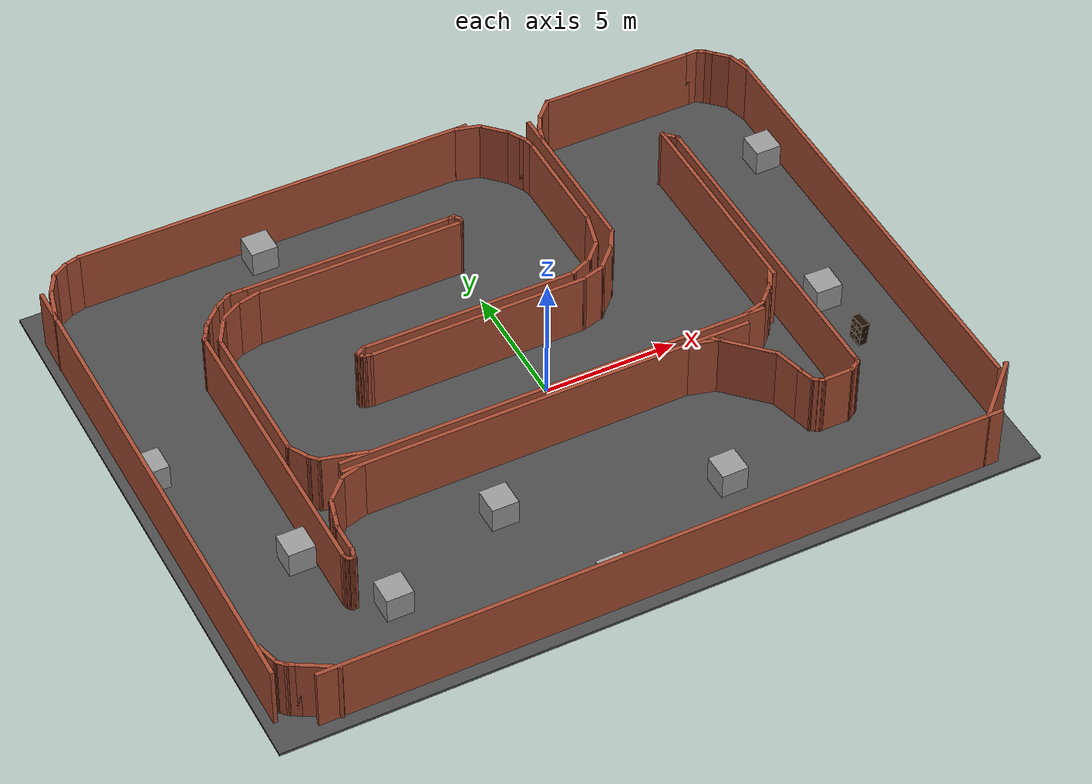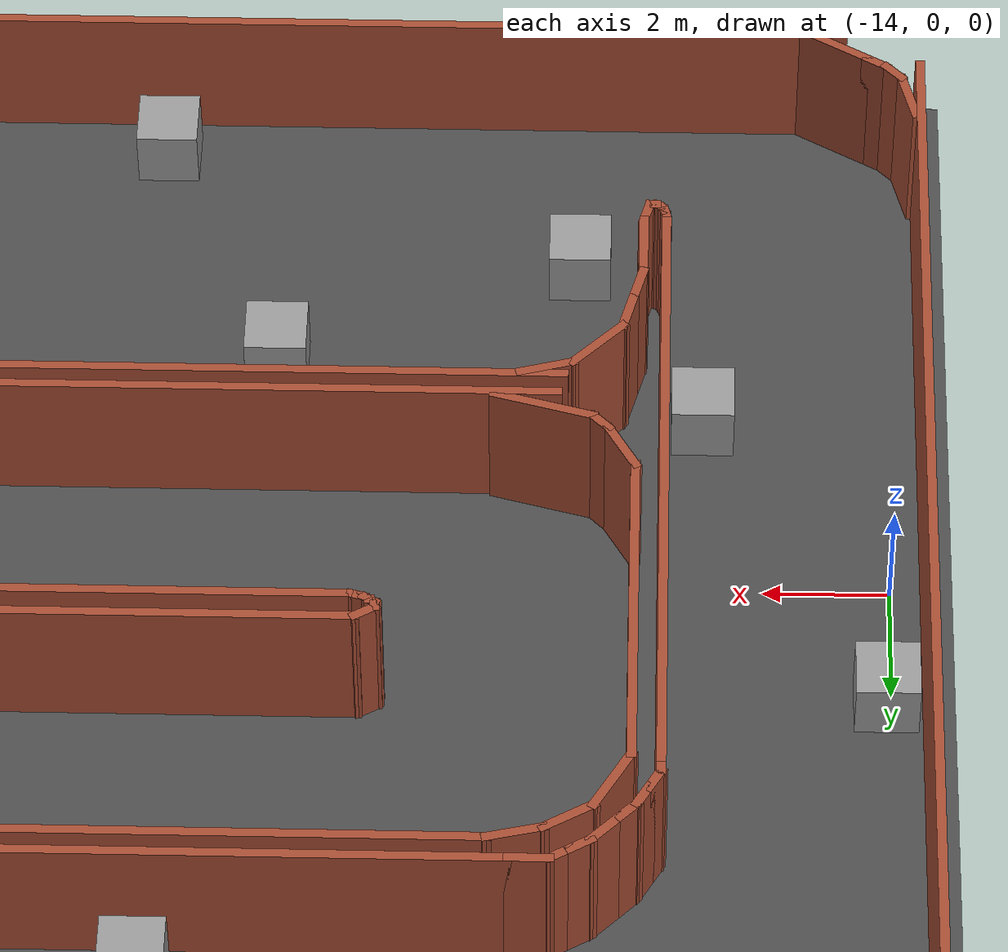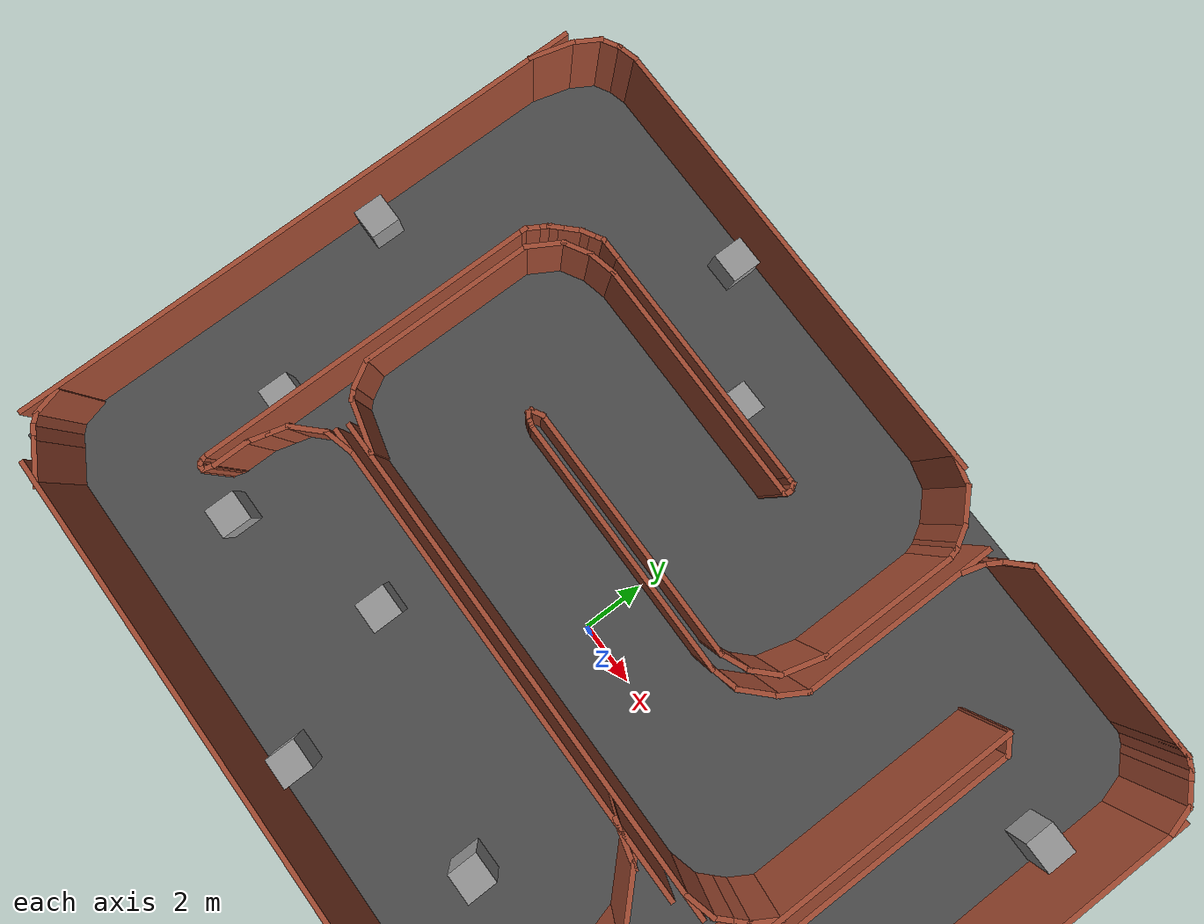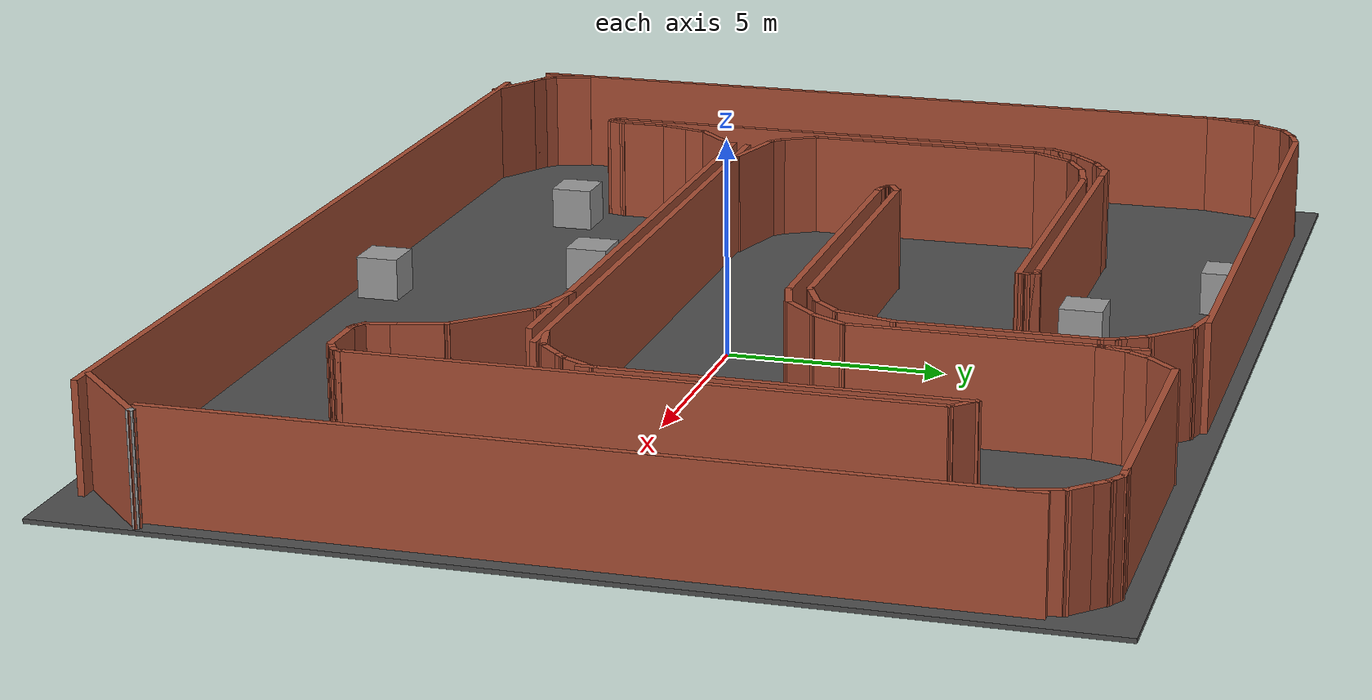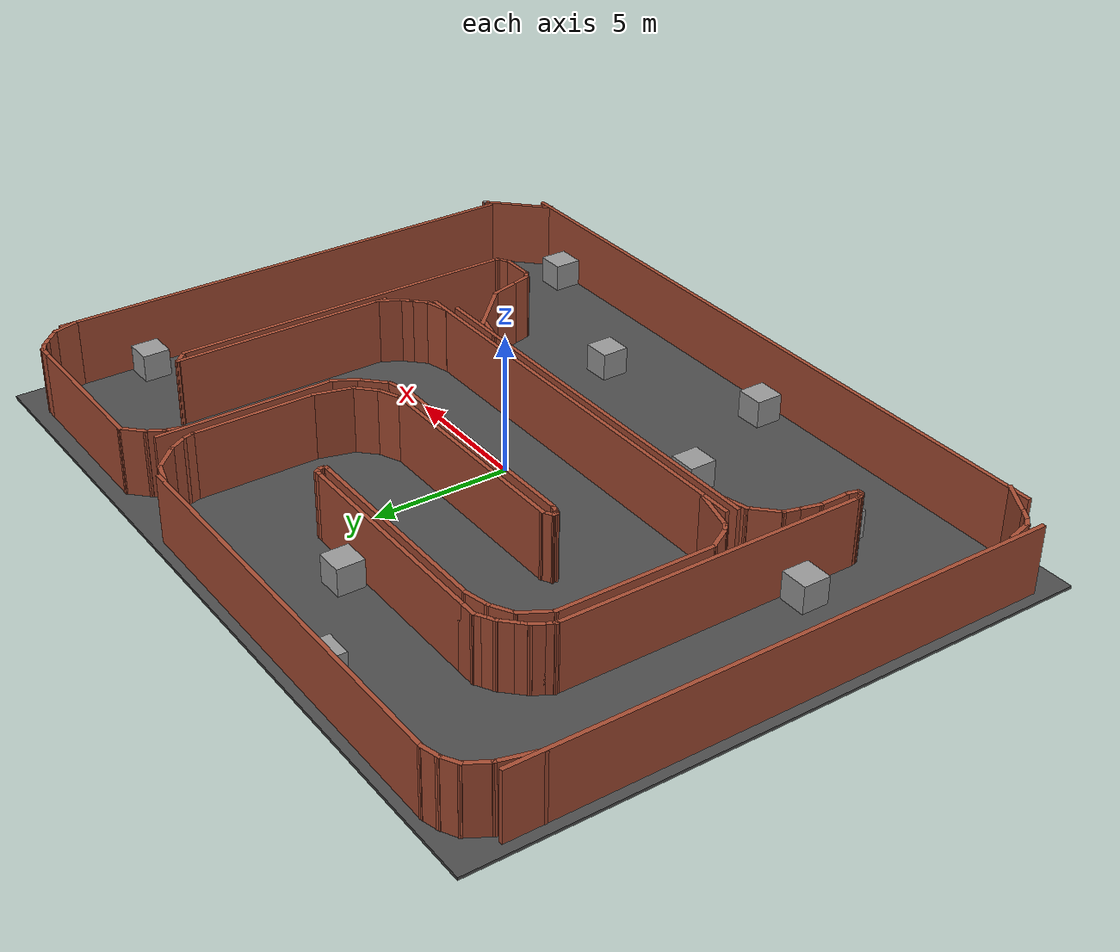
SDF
<sdf version="1.7">
 <world name="default">
  <light name="sun" type="directional">
   <pose>0 0 100 0 -0 0</pose>
   <diffuse>0.8 0.8 0.8 1</diffuse>
   <specular>0.1 0.1 0.1 1</specular>
   <attenuation>
    <range>1000</range>
    <constant>0.9</constant>
    <linear>0.01</linear>
    <quadratic>0.001</quadratic>
   </attenuation>
   <direction>-0.5 0.5 -1</direction>
   <spot><inner_angle>0</inner_angle><outer_angle>0</outer_angle><falloff>0</falloff></spot>
  </light>
  <gravity>0 0 -9.8</gravity>
  <magnetic_field>6e-06 2.3e-05 -4.2e-05</magnetic_field>
  <atmosphere type="adiabatic"/>
  <physics name="default_physics" default="0" type="ode">
   <max_step_size>0.001</max_step_size>
   <real_time_factor>1</real_time_factor>
   <real_time_update_rate>1000</real_time_update_rate>
  </physics>
  <scene><ambient>0.4 0.4 0.4 1</ambient><background>0.7 0.7 0.7 1</background><shadows>1</shadows></scene>
  <spherical_coordinates>
   <surface_model>EARTH_WGS84</surface_model>
   <latitude_deg>0</latitude_deg>
   <longitude_deg>0</longitude_deg>
   <elevation>0</elevation>
   <heading_deg>0</heading_deg>
  </spherical_coordinates>
  <model name="asphalt_plane">
   <static>1</static>
   <link name="link">
    <collision name="collision"><geometry><box><size>28.54 22.04 0.1</size></box></geometry></collision>
    <visual name="visual">
     <cast_shadows>0</cast_shadows>
     <geometry><box><size>28.54 22.04 0.1</size></box></geometry>
     <material>
      <script>
       <uri>model://asphalt_plane/materials/scripts</uri>
       <uri>model://asphalt_plane/materials/textures</uri>
       <name>vrc/asphalt</name>
      </script>
     </material>
    </visual>
   </link>
   <pose>-0.714703 0.532706 0 0 -0 0</pose>
  </model>
  <audio><device>default</device></audio>
  <model name="unit_box_clone">
   <pose>-9.03001 -6.55583 0.550002 -4e-06 -0 0.000138</pose>
   <link name="link">
    <inertial>
     <mass>1</mass>
     <inertia>
      <ixx>0.166667</ixx>
      <ixy>0</ixy>
      <ixz>0</ixz>
      <iyy>0.166667</iyy>
      <iyz>0</iyz>
      <izz>0.166667</izz>
     </inertia>
    </inertial>
    <collision name="collision"><geometry><box><size>1 1 1</size></box></geometry></collision>
    <visual name="visual">
     <geometry><box><size>1 1 1</size></box></geometry>
     <material>
      <script><name>Gazebo/Grey</name><uri>file://media/materials/scripts/gazebo.material</uri></script>
     </material>
    </visual>
   </link>
  </model>
  <model name="unit_box_clone_0">
   <pose>-2.13913 -9.08253 0.550002 -4e-06 -0 0.000121</pose>
   <link name="link">
    <inertial>
     <mass>1</mass>
     <inertia>
      <ixx>0.166667</ixx>
      <ixy>0</ixy>
      <ixz>0</ixz>
      <iyy>0.166667</iyy>
      <iyz>0</iyz>
      <izz>0.166667</izz>
     </inertia>
    </inertial>
    <collision name="collision"><geometry><box><size>1 1 1</size></box></geometry></collision>
    <visual name="visual">
     <geometry><box><size>1 1 1</size></box></geometry>
     <material>
      <script><name>Gazebo/Grey</name><uri>file://media/materials/scripts/gazebo.material</uri></script>
     </material>
    </visual>
   </link>
  </model>
  <model name="unit_box_clone_2">
   <pose>10.7393 -0.480068 0.549996 0 9e-06 -0.029689</pose>
   <link name="link">
    <inertial>
     <mass>1</mass>
     <inertia>
      <ixx>0.166667</ixx>
      <ixy>0</ixy>
      <ixz>0</ixz>
      <iyy>0.166667</iyy>
      <iyz>0</iyz>
      <izz>0.166667</izz>
     </inertia>
    </inertial>
    <collision name="collision"><geometry><box><size>1 1 1</size></box></geometry></collision>
    <visual name="visual">
     <geometry><box><size>1 1 1</size></box></geometry>
     <material>
      <script><name>Gazebo/Grey</name><uri>file://media/materials/scripts/gazebo.material</uri></script>
     </material>
    </visual>
   </link>
  </model>
  <model name="unit_box_clone_5">
   <pose>10.0295 -9.35501 0.55 0 -0 5.5e-05</pose>
   <link name="link">
    <inertial>
     <mass>1</mass>
     <inertia>
      <ixx>0.166667</ixx>
      <ixy>0</ixy>
      <ixz>0</ixz>
      <iyy>0.166667</iyy>
      <iyz>0</iyz>
      <izz>0.166667</izz>
     </inertia>
    </inertial>
    <collision name="collision"><geometry><box><size>1 1 1</size></box></geometry></collision>
    <visual name="visual">
     <geometry><box><size>1 1 1</size></box></geometry>
     <material>
      <script><name>Gazebo/Grey</name><uri>file://media/materials/scripts/gazebo.material</uri></script>
     </material>
    </visual>
   </link>
  </model>
  <model name="unit_box_clone_9">
   <pose>12.4219 6.83816 0.550002 -4e-06 -0 0.000108</pose>
   <link name="link">
    <inertial>
     <mass>1</mass>
     <inertia>
      <ixx>0.166667</ixx>
      <ixy>0</ixy>
      <ixz>0</ixz>
      <iyy>0.166667</iyy>
      <iyz>0</iyz>
      <izz>0.166667</izz>
     </inertia>
    </inertial>
    <collision name="collision"><geometry><box><size>1 1 1</size></box></geometry></collision>
    <visual name="visual">
     <geometry><box><size>1 1 1</size></box></geometry>
     <material>
      <script><name>Gazebo/Grey</name><uri>file://media/materials/scripts/gazebo.material</uri></script>
     </material>
    </visual>
   </link>
  </model>
  <model name="unit_box_clone_11">
   <pose>-2.61689 7.65173 0.550002 -4e-06 -0 0.000139</pose>
   <link name="link">
    <inertial>
     <mass>1</mass>
     <inertia>
      <ixx>0.166667</ixx>
      <ixy>0</ixy>
      <ixz>0</ixz>
      <iyy>0.166667</iyy>
      <iyz>0</iyz>
      <izz>0.166667</izz>
     </inertia>
    </inertial>
    <collision name="collision"><geometry><box><size>1 1 1</size></box></geometry></collision>
    <visual name="visual">
     <geometry><box><size>1 1 1</size></box></geometry>
     <material>
      <script><name>Gazebo/Grey</name><uri>file://media/materials/scripts/gazebo.material</uri></script>
     </material>
    </visual>
   </link>
  </model>
  <model name="unit_box_clone_12">
   <pose>-6.20194 10.3429 0.550002 -4e-06 -0 0.000137</pose>
   <link name="link">
    <inertial>
     <mass>1</mass>
     <inertia>
      <ixx>0.166667</ixx>
      <ixy>0</ixy>
      <ixz>0</ixz>
      <iyy>0.166667</iyy>
      <iyz>0</iyz>
      <izz>0.166667</izz>
     </inertia>
    </inertial>
    <collision name="collision"><geometry><box><size>1 1 1</size></box></geometry></collision>
    <visual name="visual">
     <geometry><box><size>1 1 1</size></box></geometry>
     <material>
      <script><name>Gazebo/Grey</name><uri>file://media/materials/scripts/gazebo.material</uri></script>
     </material>
    </visual>
   </link>
  </model>
  <model name="unit_box_clone_14">
   <pose>-13.9085 2.23417 0.550002 -4e-06 -0 0.000119</pose>
   <link name="link">
    <inertial>
     <mass>1</mass>
     <inertia>
      <ixx>0.166667</ixx>
      <ixy>0</ixy>
      <ixz>0</ixz>
      <iyy>0.166667</iyy>
      <iyz>0</iyz>
      <izz>0.166667</izz>
     </inertia>
    </inertial>
    <collision name="collision"><geometry><box><size>1 1 1</size></box></geometry></collision>
    <visual name="visual">
     <geometry><box><size>1 1 1</size></box></geometry>
     <material>
      <script><name>Gazebo/Grey</name><uri>file://media/materials/scripts/gazebo.material</uri></script>
     </material>
    </visual>
   </link>
  </model>
  <model name="unit_box_clone_16">
   <pose>-11.0431 -3.28249 0.550002 -4e-06 -0 0.000131</pose>
   <link name="link">
    <inertial>
     <mass>1</mass>
     <inertia>
      <ixx>0.166667</ixx>
      <ixy>0</ixy>
      <ixz>0</ixz>
      <iyy>0.166667</iyy>
      <iyz>0</iyz>
      <izz>0.166667</izz>
     </inertia>
    </inertial>
    <collision name="collision"><geometry><box><size>1 1 1</size></box></geometry></collision>
    <visual name="visual">
     <geometry><box><size>1 1 1</size></box></geometry>
     <material>
      <script><name>Gazebo/Grey</name><uri>file://media/materials/scripts/gazebo.material</uri></script>
     </material>
    </visual>
   </link>
  </model>
  <model name="unit_box_clone_clone">
   <pose>-4.15825 -4.55218 0.550002 -4e-06 -0 0.000142</pose>
   <link name="link">
    <inertial>
     <mass>1</mass>
     <inertia>
      <ixx>0.166667</ixx>
      <ixy>0</ixy>
      <ixz>0</ixz>
      <iyy>0.166667</iyy>
      <iyz>0</iyz>
      <izz>0.166667</izz>
     </inertia>
    </inertial>
    <collision name="collision"><geometry><box><size>1 1 1</size></box></geometry></collision>
    <visual name="visual">
     <geometry><box><size>1 1 1</size></box></geometry>
     <material>
      <script><name>Gazebo/Grey</name><uri>file://media/materials/scripts/gazebo.material</uri></script>
     </material>
    </visual>
   </link>
  </model>
  <model name="unit_box_clone_clone_clone">
   <pose>3.42763 -6.6926 0.550002 -4e-06 0 0.010133</pose>
   <link name="link">
    <inertial>
     <mass>1</mass>
     <inertia>
      <ixx>0.166667</ixx>
      <ixy>0</ixy>
      <ixz>0</ixz>
      <iyy>0.166667</iyy>
      <iyz>0</iyz>
      <izz>0.166667</izz>
     </inertia>
    </inertial>
    <collision name="collision"><geometry><box><size>1 1 1</size></box></geometry></collision>
    <visual name="visual">
     <geometry><box><size>1 1 1</size></box></geometry>
     <material>
      <script><name>Gazebo/Grey</name><uri>file://media/materials/scripts/gazebo.material</uri></script>
     </material>
    </visual>
   </link>
  </model>
  <model name="Untitled_0">
   <pose>2.17229 1.41798 0 0 -0 0</pose>
   <link name="Wall_100">
    <collision name="Wall_100_Collision">
     <geometry><box><size>0.5 0.15 2.5</size></box></geometry>
     <pose>0 0 1.25 0 -0 0</pose>
    </collision>
    <visual name="Wall_100_Visual">
     <pose>0 0 1.25 0 -0 0</pose>
     <geometry><box><size>0.5 0.15 2.5</size></box></geometry>
     <material>
      <script><uri>file://media/materials/scripts/gazebo.material</uri><name>Gazebo/Bricks</name></script>
      <ambient>1 1 1 1</ambient>
     </material>
     <meta><layer>0</layer></meta>
    </visual>
    <pose>9.51531 9.51082 0 0 -0 0</pose>
   </link>
   <link name="Wall_101">
    <collision name="Wall_101_Collision">
     <geometry><box><size>0.5 0.15 2.5</size></box></geometry>
     <pose>0 0 1.25 0 -0 0</pose>
    </collision>
    <visual name="Wall_101_Visual">
     <pose>0 0 1.25 0 -0 0</pose>
     <geometry><box><size>0.5 0.15 2.5</size></box></geometry>
     <material>
      <script><uri>file://media/materials/scripts/gazebo.material</uri><name>Gazebo/Bricks</name></script>
      <ambient>1 1 1 1</ambient>
     </material>
     <meta><layer>0</layer></meta>
    </visual>
    <pose>9.84186 9.42332 0 0 -0 -0.523599</pose>
   </link>
   <link name="Wall_102">
    <collision name="Wall_102_Collision">
     <geometry><box><size>0.5 0.15 2.5</size></box></geometry>
     <pose>0 0 1.25 0 -0 0</pose>
    </collision>
    <visual name="Wall_102_Visual">
     <pose>0 0 1.25 0 -0 0</pose>
     <geometry><box><size>0.5 0.15 2.5</size></box></geometry>
     <material>
      <script><uri>file://media/materials/scripts/gazebo.material</uri><name>Gazebo/Bricks</name></script>
      <ambient>1 1 1 1</ambient>
     </material>
     <meta><layer>0</layer></meta>
    </visual>
    <pose>10.1172 9.21208 0 0 -0 -0.785398</pose>
   </link>
   <link name="Wall_103">
    <collision name="Wall_103_Collision">
     <geometry><box><size>0.75 0.15 2.5</size></box></geometry>
     <pose>0 0 1.25 0 -0 0</pose>
    </collision>
    <visual name="Wall_103_Visual">
     <pose>0 0 1.25 0 -0 0</pose>
     <geometry><box><size>0.75 0.15 2.5</size></box></geometry>
     <material>
      <script><uri>file://media/materials/scripts/gazebo.material</uri><name>Gazebo/Bricks</name></script>
      <ambient>1 1 1 1</ambient>
     </material>
     <meta><layer>0</layer></meta>
    </visual>
    <pose>10.453 8.8762 0 0 -0 -0.785398</pose>
   </link>
   <link name="Wall_104">
    <collision name="Wall_104_Collision">
     <geometry><box><size>1 0.15 2.5</size></box></geometry>
     <pose>0 0 1.25 0 -0 0</pose>
    </collision>
    <visual name="Wall_104_Visual">
     <pose>0 0 1.25 0 -0 0</pose>
     <geometry><box><size>1 0.15 2.5</size></box></geometry>
     <material>
      <script><uri>file://media/materials/scripts/gazebo.material</uri><name>Gazebo/Bricks</name></script>
      <ambient>1 1 1 1</ambient>
     </material>
     <meta><layer>0</layer></meta>
    </visual>
    <pose>10.7752 8.25355 0 0 -0 -1.309</pose>
   </link>
   <link name="Wall_73">
    <collision name="Wall_73_Collision">
     <geometry><box><size>16.25 0.15 2.5</size></box></geometry>
     <pose>0 0 1.25 0 -0 0</pose>
    </collision>
    <visual name="Wall_73_Visual">
     <pose>0 0 1.25 0 -0 0</pose>
     <geometry><box><size>16.25 0.15 2.5</size></box></geometry>
     <material>
      <script><uri>file://media/materials/scripts/gazebo.material</uri><name>Gazebo/Bricks</name></script>
      <ambient>1 1 1 1</ambient>
     </material>
     <meta><layer>0</layer></meta>
    </visual>
    <pose>-2.86052 -3.41043 0 0 -0 0</pose>
   </link>
   <link name="Wall_76">
    <collision name="Wall_76_Collision">
     <geometry><box><size>8.25 0.15 2.5</size></box></geometry>
     <pose>0 0 1.25 0 -0 0</pose>
    </collision>
    <visual name="Wall_76_Visual">
     <pose>0 0 1.25 0 -0 0</pose>
     <geometry><box><size>8.25 0.15 2.5</size></box></geometry>
     <material>
      <script><uri>file://media/materials/scripts/gazebo.material</uri><name>Gazebo/Bricks</name></script>
      <ambient>1 1 1 1</ambient>
     </material>
     <meta><layer>0</layer></meta>
    </visual>
    <pose>-3.69073 0.69136 0 0 -0 0</pose>
   </link>
   <link name="Wall_78">
    <collision name="Wall_78_Collision">
     <geometry><box><size>1 0.15 2.5</size></box></geometry>
     <pose>0 0 1.25 0 -0 0</pose>
    </collision>
    <visual name="Wall_78_Visual">
     <pose>0 0 1.25 0 -0 0</pose>
     <geometry><box><size>1 0.15 2.5</size></box></geometry>
     <material>
      <script><uri>file://media/materials/scripts/gazebo.material</uri><name>Gazebo/Bricks</name></script>
      <ambient>1 1 1 1</ambient>
     </material>
     <meta><layer>0</layer></meta>
    </visual>
    <pose>0.769793 0.801358 0 0 -0 0.261799</pose>
   </link>
   <link name="Wall_79">
    <collision name="Wall_79_Collision">
     <geometry><box><size>1.25 0.15 2.5</size></box></geometry>
     <pose>0 0 1.25 0 -0 0</pose>
    </collision>
    <visual name="Wall_79_Visual">
     <pose>0 0 1.25 0 -0 0</pose>
     <geometry><box><size>1.25 0.15 2.5</size></box></geometry>
     <material>
      <script><uri>file://media/materials/scripts/gazebo.material</uri><name>Gazebo/Bricks</name></script>
      <ambient>1 1 1 1</ambient>
     </material>
     <meta><layer>0</layer></meta>
    </visual>
    <pose>1.56922 1.30027 0 0 -0 0.785398</pose>
   </link>
   <link name="Wall_80">
    <collision name="Wall_80_Collision">
     <geometry><box><size>1 0.15 2.5</size></box></geometry>
     <pose>0 0 1.25 0 -0 0</pose>
    </collision>
    <visual name="Wall_80_Visual">
     <pose>0 0 1.25 0 -0 0</pose>
     <geometry><box><size>1 0.15 2.5</size></box></geometry>
     <material>
      <script><uri>file://media/materials/scripts/gazebo.material</uri><name>Gazebo/Bricks</name></script>
      <ambient>1 1 1 1</ambient>
     </material>
     <meta><layer>0</layer></meta>
    </visual>
    <pose>2.17063 2.05723 0 0 -0 1.0472</pose>
   </link>
   <link name="Wall_81">
    <collision name="Wall_81_Collision">
     <geometry><box><size>6.5 0.15 2.5</size></box></geometry>
     <pose>0 0 1.25 0 -0 0</pose>
    </collision>
    <visual name="Wall_81_Visual">
     <pose>0 0 1.25 0 -0 0</pose>
     <geometry><box><size>6.5 0.15 2.5</size></box></geometry>
     <material>
      <script><uri>file://media/materials/scripts/gazebo.material</uri><name>Gazebo/Bricks</name></script>
      <ambient>1 1 1 1</ambient>
     </material>
     <meta><layer>0</layer></meta>
    </visual>
    <pose>2.38313 5.6003 0 0 -0 1.5708</pose>
   </link>
   <link name="Wall_83">
    <collision name="Wall_83_Collision">
     <geometry><box><size>8.25 0.15 2.5</size></box></geometry>
     <pose>0 0 1.25 0 -0 0</pose>
    </collision>
    <visual name="Wall_83_Visual">
     <pose>0 0 1.25 0 -0 0</pose>
     <geometry><box><size>8.25 0.15 2.5</size></box></geometry>
     <material>
      <script><uri>file://media/materials/scripts/gazebo.material</uri><name>Gazebo/Bricks</name></script>
      <ambient>1 1 1 1</ambient>
     </material>
     <meta><layer>0</layer></meta>
    </visual>
    <pose>6.40756 2.01956 0 0 -0 -1.5708</pose>
   </link>
   <link name="Wall_87">
    <collision name="Wall_87_Collision">
     <geometry><box><size>1 0.15 2.5</size></box></geometry>
     <pose>0 0 1.25 0 -0 0</pose>
    </collision>
    <visual name="Wall_87_Visual">
     <pose>0 0 1.25 0 -0 0</pose>
     <geometry><box><size>1 0.15 2.5</size></box></geometry>
     <material>
      <script><uri>file://media/materials/scripts/gazebo.material</uri><name>Gazebo/Bricks</name></script>
      <ambient>1 1 1 1</ambient>
     </material>
     <meta><layer>0</layer></meta>
    </visual>
    <pose>4.90949 -3.27284 0 0 -0 0.261799</pose>
   </link>
   <link name="Wall_88">
    <collision name="Wall_88_Collision">
     <geometry><box><size>0.75 0.15 2.5</size></box></geometry>
     <pose>0 0 1.25 0 -0 0</pose>
    </collision>
    <visual name="Wall_88_Visual">
     <pose>0 0 1.25 0 -0 0</pose>
     <geometry><box><size>0.75 0.15 2.5</size></box></geometry>
     <material>
      <script><uri>file://media/materials/scripts/gazebo.material</uri><name>Gazebo/Bricks</name></script>
      <ambient>1 1 1 1</ambient>
     </material>
     <meta><layer>0</layer></meta>
    </visual>
    <pose>5.53214 -2.95071 0 0 -0 0.785398</pose>
   </link>
   <link name="Wall_89">
    <collision name="Wall_89_Collision">
     <geometry><box><size>0.5 0.15 2.5</size></box></geometry>
     <pose>0 0 1.25 0 -0 0</pose>
    </collision>
    <visual name="Wall_89_Visual">
     <pose>0 0 1.25 0 -0 0</pose>
     <geometry><box><size>0.5 0.15 2.5</size></box></geometry>
     <material>
      <script><uri>file://media/materials/scripts/gazebo.material</uri><name>Gazebo/Bricks</name></script>
      <ambient>1 1 1 1</ambient>
     </material>
     <meta><layer>0</layer></meta>
    </visual>
    <pose>5.86801 -2.61483 0 0 -0 0.785398</pose>
   </link>
   <link name="Wall_90">
    <collision name="Wall_90_Collision">
     <geometry><box><size>1 0.15 2.5</size></box></geometry>
     <pose>0 0 1.25 0 -0 0</pose>
    </collision>
    <visual name="Wall_90_Visual">
     <pose>0 0 1.25 0 -0 0</pose>
     <geometry><box><size>1 0.15 2.5</size></box></geometry>
     <material>
      <script><uri>file://media/materials/scripts/gazebo.material</uri><name>Gazebo/Bricks</name></script>
      <ambient>1 1 1 1</ambient>
     </material>
     <meta><layer>0</layer></meta>
    </visual>
    <pose>6.20426 -2.12303 0 0 -0 1.0472</pose>
   </link>
   <link name="Wall_92">
    <collision name="Wall_92_Collision">
     <geometry><box><size>18 0.15 2.5</size></box></geometry>
     <pose>0 0 1.2495 0 -0 0</pose>
    </collision>
    <visual name="Wall_92_Visual">
     <pose>0 0 1.2495 0 -0 0</pose>
     <geometry><box><size>18 0.15 2.5</size></box></geometry>
     <material>
      <script><uri>file://media/materials/scripts/gazebo.material</uri><name>Gazebo/Bricks</name></script>
      <ambient>1 1 1 1</ambient>
     </material>
     <meta><layer>0</layer></meta>
    </visual>
    <pose>10.9105 -0.616886 0 0 -0 -1.5708</pose>
   </link>
   <link name="Wall_95">
    <collision name="Wall_95_Collision">
     <geometry><box><size>0.75 0.15 2.5</size></box></geometry>
     <pose>0 0 1.25 0 -0 0</pose>
    </collision>
    <visual name="Wall_95_Visual">
     <pose>0 0 1.25 0 -0 0</pose>
     <geometry><box><size>0.75 0.15 2.5</size></box></geometry>
     <material>
      <script><uri>file://media/materials/scripts/gazebo.material</uri><name>Gazebo/Bricks</name></script>
      <ambient>1 1 1 1</ambient>
     </material>
     <meta><layer>0</layer></meta>
    </visual>
    <pose>2.51162 8.10039 0 0 -0 1.309</pose>
   </link>
   <link name="Wall_96">
    <collision name="Wall_96_Collision">
     <geometry><box><size>0.75 0.15 2.5</size></box></geometry>
     <pose>0 0 1.25 0 -0 0</pose>
    </collision>
    <visual name="Wall_96_Visual">
     <pose>0 0 1.25 0 -0 0</pose>
     <geometry><box><size>0.75 0.15 2.5</size></box></geometry>
     <material>
      <script><uri>file://media/materials/scripts/gazebo.material</uri><name>Gazebo/Bricks</name></script>
      <ambient>1 1 1 1</ambient>
     </material>
     <meta><layer>0</layer></meta>
    </visual>
    <pose>2.73927 8.64997 0 0 -0 1.0472</pose>
   </link>
   <link name="Wall_98">
    <collision name="Wall_98_Collision">
     <geometry><box><size>1 0.15 2.5</size></box></geometry>
     <pose>0 0 1.25 0 -0 0</pose>
    </collision>
    <visual name="Wall_98_Visual">
     <pose>0 0 1.25 0 -0 0</pose>
     <geometry><box><size>1 0.15 2.5</size></box></geometry>
     <material>
      <script><uri>file://media/materials/scripts/gazebo.material</uri><name>Gazebo/Bricks</name></script>
      <ambient>1 1 1 1</ambient>
     </material>
     <meta><layer>0</layer></meta>
    </visual>
    <pose>3.18979 9.2103 0 0 -0 0.785398</pose>
   </link>
   <link name="Wall_99">
    <collision name="Wall_99_Collision">
     <geometry><box><size>6 0.15 2.5</size></box></geometry>
     <pose>0 0 1.25 0 -0 0</pose>
    </collision>
    <visual name="Wall_99_Visual">
     <pose>0 0 1.25 0 -0 0</pose>
     <geometry><box><size>6 0.15 2.5</size></box></geometry>
     <material>
      <script><uri>file://media/materials/scripts/gazebo.material</uri><name>Gazebo/Bricks</name></script>
      <ambient>1 1 1 1</ambient>
     </material>
     <meta><layer>0</layer></meta>
    </visual>
    <pose>6.41531 9.51082 0 0 -0 0</pose>
   </link>
   <static>1</static>
  </model>
  <model name="Untitled">
   <pose>-1.155 -1.2225 0 0 -0 0</pose>
   <link name="Wall_0">
    <collision name="Wall_0_Collision">
     <geometry><box><size>15.5 0.15 2.5</size></box></geometry>
     <pose>0 0 1.25 0 -0 0</pose>
    </collision>
    <visual name="Wall_0_Visual">
     <pose>0 0 1.25 0 -0 0</pose>
     <geometry><box><size>15.5 0.15 2.5</size></box></geometry>
     <material>
      <script><uri>file://media/materials/scripts/gazebo.material</uri><name>Gazebo/Bricks</name></script>
      <ambient>1 1 1 1</ambient>
     </material>
     <meta><layer>0</layer></meta>
    </visual>
    <pose>-0 -1.1475 0 0 -0 0</pose>
   </link>
   <static>1</static>
  </model>
  <model name="Untitled_1">
   <pose>4.54374 0.998214 0 0 -0 0</pose>
   <link name="Wall_3">
    <collision name="Wall_3_Collision">
     <geometry><box><size>12.75 0.15 2.5</size></box></geometry>
     <pose>0 0 1.25 0 -0 0</pose>
    </collision>
    <visual name="Wall_3_Visual">
     <pose>0 0 1.25 0 -0 0</pose>
     <geometry><box><size>12.75 0.15 2.5</size></box></geometry>
     <material>
      <script><uri>file://media/materials/scripts/gazebo.material</uri><name>Gazebo/Bricks</name></script>
      <ambient>1 1 1 1</ambient>
     </material>
     <meta><layer>0</layer></meta>
    </visual>
    <pose>4.43768 -0.227665 0 0 -0 1.5708</pose>
   </link>
   <link name="Wall_5">
    <collision name="Wall_5_Collision">
     <geometry><box><size>0.75 0.15 2.5</size></box></geometry>
     <pose>0 0 1.25 0 -0 0</pose>
    </collision>
    <visual name="Wall_5_Visual">
     <pose>0 0 1.25 0 -0 0</pose>
     <geometry><box><size>0.75 0.15 2.5</size></box></geometry>
     <material>
      <script><uri>file://media/materials/scripts/gazebo.material</uri><name>Gazebo/Bricks</name></script>
      <ambient>1 1 1 1</ambient>
     </material>
     <meta><layer>0</layer></meta>
    </visual>
    <pose>4.22555 6.28447 0 0 -0 2.35619</pose>
   </link>
   <static>1</static>
  </model>
  <model name="6_Cube_StorageE">
   <link name="Wall_0">
    <pose>0 0 0.01 0 -0 0</pose>
    <inertial>
     <mass>1.6201</mass>
     <inertia><ixx>0.0119</ixx><iyy>0.0631</iyy><izz>0.0513</izz><ixy>0</ixy><ixz>0</ixz><iyz>0</iyz></inertia>
    </inertial>
    <collision name="Wall_0_Collision"><geometry><box><size>0.616 0.296 0.02</size></box></geometry></collision>
    <visual name="Wall_0_Visual">
     <geometry><box><size>0.616 0.296 0.02</size></box></geometry>
     <material>
      <script><uri>file://media/materials/scripts/gazebo.material</uri><name>Gazebo/Grey</name></script>
      <ambient>0.105882 0.0509804 0 1</ambient>
     </material>
    </visual>
   </link>
   <joint name="0_2" type="fixed">
    <pose>-0.308 0 0 0 -0 0</pose>
    <parent>Wall_2</parent>
    <child>Wall_0</child>
    <axis><xyz>1 0 0</xyz><limit><lower>-1e+16</lower><upper>1e+16</upper></limit></axis>
   </joint>
   <joint name="0_12" type="fixed">
    <parent>Wall_12</parent>
    <child>Wall_0</child>
    <axis><xyz>0 0 1</xyz><limit><lower>-1e+16</lower><upper>1e+16</upper></limit></axis>
   </joint>
   <joint name="0_4" type="fixed">
    <pose>0.308 0 0 0 -0 0</pose>
    <parent>Wall_4</parent>
    <child>Wall_0</child>
    <axis><xyz>1 0 0</xyz><limit><lower>-1e+16</lower><upper>1e+16</upper></limit></axis>
   </joint>
   <link name="Wall_10">
    <pose>0 0 0.61 0 -0 0</pose>
    <inertial>
     <mass>1.6201</mass>
     <inertia><ixx>0.0119</ixx><iyy>0.0631</iyy><izz>0.0513</izz><ixy>0</ixy><ixz>0</ixz><iyz>0</iyz></inertia>
    </inertial>
    <collision name="Wall_10_Collision"><geometry><box><size>0.616 0.296 0.02</size></box></geometry></collision>
    <visual name="Wall_10_Visual">
     <geometry><box><size>0.616 0.296 0.02</size></box></geometry>
     <material>
      <script><uri>file://media/materials/scripts/gazebo.material</uri><name>Gazebo/Grey</name></script>
      <ambient>0.105882 0.0509804 0 1</ambient>
     </material>
    </visual>
   </link>
   <joint name="10_2" type="fixed">
    <pose>-0.308 0 0 0 -0 0</pose>
    <parent>Wall_2</parent>
    <child>Wall_10</child>
    <axis><xyz>1 0 0</xyz><limit><lower>-1e+16</lower><upper>1e+16</upper></limit></axis>
   </joint>
   <joint name="10_12" type="fixed">
    <parent>Wall_12</parent>
    <child>Wall_10</child>
    <axis><xyz>0 0 1</xyz><limit><lower>-1e+16</lower><upper>1e+16</upper></limit></axis>
   </joint>
   <joint name="10_4" type="fixed">
    <pose>0.308 0 0 0 -0 0</pose>
    <parent>Wall_4</parent>
    <child>Wall_10</child>
    <axis><xyz>1 0 0</xyz><limit><lower>-1e+16</lower><upper>1e+16</upper></limit></axis>
   </joint>
   <link name="Wall_12">
    <pose>0 0 0.4575 0 -0 0</pose>
    <inertial>
     <mass>2.4065</mass>
     <inertia><ixx>0.0177</ixx><iyy>0.1855</iyy><izz>0.168</izz><ixy>0</ixy><ixz>0</ixz><iyz>0</iyz></inertia>
    </inertial>
    <collision name="Wall_12_Collision"><geometry><box><size>0.02 0.296 0.915</size></box></geometry></collision>
    <visual name="Wall_12_Visual">
     <geometry><box><size>0.02 0.296 0.915</size></box></geometry>
     <material>
      <script><uri>file://media/materials/scripts/gazebo.material</uri><name>Gazebo/Grey</name></script>
      <ambient>0.105882 0.0509804 0 1</ambient>
     </material>
    </visual>
   </link>
   <link name="Wall_2">
    <pose>-0.298 0 0.4575 0 -0 0</pose>
    <inertial>
     <mass>2.4065</mass>
     <inertia><ixx>0.0177</ixx><iyy>0.1855</iyy><izz>0.168</izz><ixy>0</ixy><ixz>0</ixz><iyz>0</iyz></inertia>
    </inertial>
    <collision name="Wall_2_Collision"><geometry><box><size>0.02 0.296 0.915</size></box></geometry></collision>
    <visual name="Wall_2_Visual">
     <geometry><box><size>0.02 0.296 0.915</size></box></geometry>
     <material>
      <script><uri>file://media/materials/scripts/gazebo.material</uri><name>Gazebo/Grey</name></script>
      <ambient>0.105882 0.0509804 0 1</ambient>
     </material>
    </visual>
   </link>
   <link name="Wall_4">
    <pose>0.298 0 0.4575 0 -0 0</pose>
    <inertial>
     <mass>2.4065</mass>
     <inertia><ixx>0.0177</ixx><iyy>0.1855</iyy><izz>0.168</izz><ixy>0</ixy><ixz>0</ixz><iyz>0</iyz></inertia>
    </inertial>
    <collision name="Wall_4_Collision"><geometry><box><size>0.02 0.296 0.915</size></box></geometry></collision>
    <visual name="Wall_4_Visual">
     <geometry><box><size>0.02 0.296 0.915</size></box></geometry>
     <material>
      <script><uri>file://media/materials/scripts/gazebo.material</uri><name>Gazebo/Grey</name></script>
      <ambient>0.105882 0.0509804 0 1</ambient>
     </material>
    </visual>
   </link>
   <link name="Wall_6">
    <pose>0 0 0.905 0 -0 0</pose>
    <inertial>
     <mass>1.6201</mass>
     <inertia><ixx>0.0119</ixx><iyy>0.0631</iyy><izz>0.0513</izz><ixy>0</ixy><ixz>0</ixz><iyz>0</iyz></inertia>
    </inertial>
    <collision name="Wall_6_Collision"><geometry><box><size>0.616 0.296 0.02</size></box></geometry></collision>
    <visual name="Wall_6_Visual">
     <geometry><box><size>0.616 0.296 0.02</size></box></geometry>
     <material>
      <script><uri>file://media/materials/scripts/gazebo.material</uri><name>Gazebo/Grey</name></script>
      <ambient>0.105882 0.0509804 0 1</ambient>
     </material>
    </visual>
   </link>
   <joint name="6_2" type="fixed">
    <pose>-0.308 0 0 0 -0 0</pose>
    <parent>Wall_2</parent>
    <child>Wall_6</child>
    <axis><xyz>2 0 0</xyz><limit><lower>-1e+16</lower><upper>1e+16</upper></limit></axis>
   </joint>
   <joint name="6_12" type="fixed">
    <parent>Wall_12</parent>
    <child>Wall_6</child>
    <axis><xyz>0 0 1</xyz><limit><lower>-1e+16</lower><upper>1e+16</upper></limit></axis>
   </joint>
   <joint name="6_4" type="fixed">
    <pose>0.308 0 0 0 -0 0</pose>
    <parent>Wall_4</parent>
    <child>Wall_6</child>
    <axis><xyz>1 0 0</xyz><limit><lower>-1e+16</lower><upper>1e+16</upper></limit></axis>
   </joint>
   <link name="Wall_8">
    <pose>0 0 0.305 0 -0 0</pose>
    <inertial>
     <mass>1.6201</mass>
     <inertia><ixx>0.0119</ixx><iyy>0.0631</iyy><izz>0.0513</izz><ixy>0</ixy><ixz>0</ixz><iyz>0</iyz></inertia>
    </inertial>
    <collision name="Wall_8_Collision"><geometry><box><size>0.616 0.296 0.02</size></box></geometry></collision>
    <visual name="Wall_8_Visual">
     <geometry><box><size>0.616 0.296 0.02</size></box></geometry>
     <material>
      <script><uri>file://media/materials/scripts/gazebo.material</uri><name>Gazebo/Grey</name></script>
      <ambient>0.105882 0.0509804 0 1</ambient>
     </material>
    </visual>
   </link>
   <joint name="8_2" type="fixed">
    <pose>-0.308 0 0 0 -0 0</pose>
    <parent>Wall_2</parent>
    <child>Wall_8</child>
    <axis><xyz>1 0 0</xyz><limit><lower>-1e+16</lower><upper>1e+16</upper></limit></axis>
   </joint>
   <joint name="8_12" type="fixed">
    <parent>Wall_12</parent>
    <child>Wall_8</child>
    <axis><xyz>0 0 1</xyz><limit><lower>-1e+16</lower><upper>1e+16</upper></limit></axis>
   </joint>
   <joint name="8_4" type="fixed">
    <pose>0.308 0 0 0 -0 0</pose>
    <parent>Wall_4</parent>
    <child>Wall_8</child>
    <axis><xyz>1 0 0</xyz><limit><lower>-1e+16</lower><upper>1e+16</upper></limit></axis>
   </joint>
   <static>1</static>
   <pose>10.882 -2.74407 0.037123 0.078821 -0.005852 1.64475</pose>
  </model>
  <model name="Untitled_2">
   <pose>0.07367 -5.01823 0 0 -0 0</pose>
   <link name="Wall_0">
    <collision name="Wall_0_Collision">
     <geometry><box><size>25.5 0.15 2.5</size></box></geometry>
     <pose>0 0 1.25 0 -0 0</pose>
    </collision>
    <visual name="Wall_0_Visual">
     <pose>0 0 1.25 0 -0 0</pose>
     <geometry><box><size>25.5 0.15 2.5</size></box></geometry>
     <material>
      <script><uri>file://media/materials/scripts/gazebo.material</uri><name>Gazebo/Bricks</name></script>
      <ambient>1 1 1 1</ambient>
     </material>
     <meta><layer>0</layer></meta>
    </visual>
    <pose>-0.693877 -4.91181 0 0 -0 0</pose>
   </link>
   <link name="Wall_11">
    <collision name="Wall_11_Collision">
     <geometry><box><size>0.5 0.15 2.5</size></box></geometry>
     <pose>0 0 1.25 0 -0 0</pose>
    </collision>
    <visual name="Wall_11_Visual">
     <pose>0 0 1.25 0 -0 0</pose>
     <geometry><box><size>0.5 0.15 2.5</size></box></geometry>
     <material>
      <script><uri>file://media/materials/scripts/gazebo.material</uri><name>Gazebo/Bricks</name></script>
      <ambient>1 1 1 1</ambient>
     </material>
     <meta><layer>0</layer></meta>
    </visual>
    <pose>7.25302 -0.843593 0 0 -0 2.61799</pose>
   </link>
   <link name="Wall_12">
    <collision name="Wall_12_Collision">
     <geometry><box><size>0.75 0.15 2.5</size></box></geometry>
     <pose>0 0 1.25 0 -0 0</pose>
    </collision>
    <visual name="Wall_12_Visual">
     <pose>0 0 1.25 0 -0 0</pose>
     <geometry><box><size>0.75 0.15 2.5</size></box></geometry>
     <material>
      <script><uri>file://media/materials/scripts/gazebo.material</uri><name>Gazebo/Bricks</name></script>
      <ambient>1 1 1 1</ambient>
     </material>
     <meta><layer>0</layer></meta>
    </visual>
    <pose>7.02381 -0.466315 0 0 -0 1.8326</pose>
   </link>
   <link name="Wall_13">
    <collision name="Wall_13_Collision">
     <geometry><box><size>1.25 0.15 2.5</size></box></geometry>
     <pose>0 0 1.25 0 -0 0</pose>
    </collision>
    <visual name="Wall_13_Visual">
     <pose>0 0 1.25 0 -0 0</pose>
     <geometry><box><size>1.25 0.15 2.5</size></box></geometry>
     <material>
      <script><uri>file://media/materials/scripts/gazebo.material</uri><name>Gazebo/Bricks</name></script>
      <ambient>1 1 1 1</ambient>
     </material>
     <meta><layer>0</layer></meta>
    </visual>
    <pose>6.80382 0.354722 0 0 -0 1.8326</pose>
   </link>
   <link name="Wall_14">
    <collision name="Wall_14_Collision">
     <geometry><box><size>2.5 0.15 2.5</size></box></geometry>
     <pose>0 0 1.25 0 -0 0</pose>
    </collision>
    <visual name="Wall_14_Visual">
     <pose>0 0 1.25 0 -0 0</pose>
     <geometry><box><size>2.5 0.15 2.5</size></box></geometry>
     <material>
      <script><uri>file://media/materials/scripts/gazebo.material</uri><name>Gazebo/Bricks</name></script>
      <ambient>1 1 1 1</ambient>
     </material>
     <meta><layer>0</layer></meta>
    </visual>
    <pose>5.83062 1.71683 0 0 -0 2.35619</pose>
   </link>
   <link name="Wall_16">
    <collision name="Wall_16_Collision">
     <geometry><box><size>1.5 0.15 2.5</size></box></geometry>
     <pose>0 0 1.25 0 -0 0</pose>
    </collision>
    <visual name="Wall_16_Visual">
     <pose>0 0 1.25 0 -0 0</pose>
     <geometry><box><size>1.5 0.15 2.5</size></box></geometry>
     <material>
      <script><uri>file://media/materials/scripts/gazebo.material</uri><name>Gazebo/Bricks</name></script>
      <ambient>1 1 1 1</ambient>
     </material>
     <meta><layer>0</layer></meta>
    </visual>
    <pose>4.60207 2.52555 0 0 -0 2.87979</pose>
   </link>
   <link name="Wall_19">
    <collision name="Wall_19_Collision">
     <geometry><box><size>2.75 0.15 2.5</size></box></geometry>
     <pose>0 0 1.25 0 -0 0</pose>
    </collision>
    <visual name="Wall_19_Visual">
     <pose>0 0 1.25 0 -0 0</pose>
     <geometry><box><size>2.75 0.15 2.5</size></box></geometry>
     <material>
      <script><uri>file://media/materials/scripts/gazebo.material</uri><name>Gazebo/Bricks</name></script>
      <ambient>1 1 1 1</ambient>
     </material>
     <meta><layer>0</layer></meta>
    </visual>
    <pose>12.4186 -3.99292 0 0 -0 0.785398</pose>
   </link>
   <link name="Wall_20">
    <collision name="Wall_20_Collision">
     <geometry><box><size>0.15 0.15 2.5</size></box></geometry>
     <pose>0 0 1.25 0 -0 0</pose>
    </collision>
    <visual name="Wall_20_Visual">
     <pose>0 0 1.25 0 -0 0</pose>
     <geometry><box><size>0.15 0.15 2.5</size></box></geometry>
     <material>
      <script><uri>file://media/materials/scripts/gazebo.material</uri><name>Gazebo/Grey</name></script>
      <ambient>1 1 1 1</ambient>
     </material>
     <meta><layer>0</layer></meta>
    </visual>
    <pose>13.3378 -3.07368 0 0 -0 0</pose>
   </link>
   <link name="Wall_3">
    <collision name="Wall_3_Collision">
     <geometry><box><size>1.25 0.15 2.5</size></box></geometry>
     <pose>0 0 1.25 0 -0 0</pose>
    </collision>
    <visual name="Wall_3_Visual">
     <pose>0 0 1.25 0 -0 0</pose>
     <geometry><box><size>1.25 0.15 2.5</size></box></geometry>
     <material>
      <script><uri>file://media/materials/scripts/gazebo.material</uri><name>Gazebo/Bricks</name></script>
      <ambient>1 1 1 1</ambient>
     </material>
     <meta><layer>0</layer></meta>
    </visual>
    <pose>7.95457 -0.931093 0 0 -0 3.14159</pose>
   </link>
   <link name="Wall_5">
    <collision name="Wall_5_Collision">
     <geometry><box><size>0.5 0.15 2.5</size></box></geometry>
     <pose>0 0 1.25 0 -0 0</pose>
    </collision>
    <visual name="Wall_5_Visual">
     <pose>0 0 1.25 0 -0 0</pose>
     <geometry><box><size>0.5 0.15 2.5</size></box></geometry>
     <material>
      <script><uri>file://media/materials/scripts/gazebo.material</uri><name>Gazebo/Bricks</name></script>
      <ambient>1 1 1 1</ambient>
     </material>
     <meta><layer>0</layer></meta>
    </visual>
    <pose>8.65612 -0.843593 0 0 -0 0.523599</pose>
   </link>
   <link name="Wall_6">
    <collision name="Wall_6_Collision">
     <geometry><box><size>0.25 0.15 2.5</size></box></geometry>
     <pose>0 0 1.25 0 -0 0</pose>
    </collision>
    <visual name="Wall_6_Visual">
     <pose>0 0 1.25 0 -0 0</pose>
     <geometry><box><size>0.25 0.15 2.5</size></box></geometry>
     <material>
      <script><uri>file://media/materials/scripts/gazebo.material</uri><name>Gazebo/Bricks</name></script>
      <ambient>1 1 1 1</ambient>
     </material>
     <meta><layer>0</layer></meta>
    </visual>
    <pose>8.84303 -0.720738 0 0 -0 0.785398</pose>
   </link>
   <link name="Wall_7">
    <collision name="Wall_7_Collision">
     <geometry><box><size>0.25 0.15 2.5</size></box></geometry>
     <pose>0 0 1.25 0 -0 0</pose>
    </collision>
    <visual name="Wall_7_Visual">
     <pose>0 0 1.25 0 -0 0</pose>
     <geometry><box><size>0.25 0.15 2.5</size></box></geometry>
     <material>
      <script><uri>file://media/materials/scripts/gazebo.material</uri><name>Gazebo/Bricks</name></script>
      <ambient>1 1 1 1</ambient>
     </material>
     <meta><layer>0</layer></meta>
    </visual>
    <pose>8.89133 -0.637086 0 0 -0 1.309</pose>
   </link>
   <link name="Wall_9">
    <collision name="Wall_9_Collision">
     <geometry><box><size>0.25 0.15 2.5</size></box></geometry>
     <pose>0 0 1.25 0 -0 0</pose>
    </collision>
    <visual name="Wall_9_Visual">
     <pose>0 0 1.25 0 -0 0</pose>
     <geometry><box><size>0.25 0.15 2.5</size></box></geometry>
     <material>
      <script><uri>file://media/materials/scripts/gazebo.material</uri><name>Gazebo/Bricks</name></script>
      <ambient>1 1 1 1</ambient>
     </material>
     <meta><layer>0</layer></meta>
    </visual>
    <pose>7.35627 -0.918152 0 0 -0 2.87979</pose>
   </link>
   <static>1</static>
  </model>
  <model name="Untitled_3">
   <pose>-7.31397 0.360051 0 0 -0 0</pose>
   <link name="Wall_0">
    <collision name="Wall_0_Collision">
     <geometry><box><size>19.25 0.15 2.5</size></box></geometry>
     <pose>0 0 1.25 0 -0 0</pose>
    </collision>
    <visual name="Wall_0_Visual">
     <pose>0 0 1.25 0 -0 0</pose>
     <geometry><box><size>19.25 0.15 2.5</size></box></geometry>
     <material>
      <script><uri>file://media/materials/scripts/gazebo.material</uri><name>Gazebo/Bricks</name></script>
      <ambient>1 1 1 1</ambient>
     </material>
     <meta><layer>0</layer></meta>
    </visual>
    <pose>-7.23893 0 0 0 -0 -1.5708</pose>
   </link>
   <link name="Wall_2">
    <collision name="Wall_2_Collision">
     <geometry><box><size>11 0.15 2.5</size></box></geometry>
     <pose>0 0 1.25 0 -0 0</pose>
    </collision>
    <visual name="Wall_2_Visual">
     <pose>0 0 1.25 0 -0 0</pose>
     <geometry><box><size>11 0.15 2.5</size></box></geometry>
     <material>
      <script><uri>file://media/materials/scripts/gazebo.material</uri><name>Gazebo/Bricks</name></script>
      <ambient>1 1 1 1</ambient>
     </material>
     <meta><layer>0</layer></meta>
    </visual>
    <pose>-3.10649 -0.578189 0 0 -0 -1.5708</pose>
   </link>
   <static>1</static>
  </model>
  <model name="Untitled_4">
   <pose>-5.25205 -3.0446 0 0 -0 0</pose>
   <link name="Wall_0">
    <collision name="Wall_0_Collision">
     <geometry><box><size>1 0.15 2.5</size></box></geometry>
     <pose>0 0 1.25 0 -0 0</pose>
    </collision>
    <visual name="Wall_0_Visual">
     <pose>0 0 1.25 0 -0 0</pose>
     <geometry><box><size>1 0.15 2.5</size></box></geometry>
     <material>
      <script><uri>file://media/materials/scripts/gazebo.material</uri><name>Gazebo/Bricks</name></script>
      <ambient>1 1 1 1</ambient>
     </material>
     <meta><layer>0</layer></meta>
    </visual>
    <pose>-3.30821 0.542856 0 0 -0 -2.87979</pose>
   </link>
   <link name="Wall_10">
    <collision name="Wall_10_Collision">
     <geometry><box><size>0.25 0.15 2.5</size></box></geometry>
     <pose>0 0 1.25 0 -0 0</pose>
    </collision>
    <visual name="Wall_10_Visual">
     <pose>0 0 1.25 0 -0 0</pose>
     <geometry><box><size>0.25 0.15 2.5</size></box></geometry>
     <material>
      <script><uri>file://media/materials/scripts/gazebo.material</uri><name>Gazebo/Bricks</name></script>
      <ambient>1 1 1 1</ambient>
     </material>
     <meta><layer>0</layer></meta>
    </visual>
    <pose>-5.04101 -2.91715 0 0 -0 2.61799</pose>
   </link>
   <link name="Wall_11">
    <collision name="Wall_11_Collision">
     <geometry><box><size>0.25 0.15 2.5</size></box></geometry>
     <pose>0 0 1.25 0 -0 0</pose>
    </collision>
    <visual name="Wall_11_Visual">
     <pose>0 0 1.25 0 -0 0</pose>
     <geometry><box><size>0.25 0.15 2.5</size></box></geometry>
     <material>
      <script><uri>file://media/materials/scripts/gazebo.material</uri><name>Gazebo/Bricks</name></script>
      <ambient>1 1 1 1</ambient>
     </material>
     <meta><layer>0</layer></meta>
    </visual>
    <pose>-5.10931 -2.84884 0 0 -0 2.0944</pose>
   </link>
   <link name="Wall_12">
    <collision name="Wall_12_Collision">
     <geometry><box><size>0.25 0.15 2.5</size></box></geometry>
     <pose>0 0 1.25 0 -0 0</pose>
    </collision>
    <visual name="Wall_12_Visual">
     <pose>0 0 1.25 0 -0 0</pose>
     <geometry><box><size>0.25 0.15 2.5</size></box></geometry>
     <material>
      <script><uri>file://media/materials/scripts/gazebo.material</uri><name>Gazebo/Bricks</name></script>
      <ambient>1 1 1 1</ambient>
     </material>
     <meta><layer>0</layer></meta>
    </visual>
    <pose>-5.14726 -2.75725 0 0 -0 1.8326</pose>
   </link>
   <link name="Wall_3">
    <collision name="Wall_3_Collision">
     <geometry><box><size>1.25 0.15 2.5</size></box></geometry>
     <pose>0 0 1.25 0 -0 0</pose>
    </collision>
    <visual name="Wall_3_Visual">
     <pose>0 0 1.25 0 -0 0</pose>
     <geometry><box><size>1.25 0.15 2.5</size></box></geometry>
     <material>
      <script><uri>file://media/materials/scripts/gazebo.material</uri><name>Gazebo/Bricks</name></script>
      <ambient>1 1 1 1</ambient>
     </material>
     <meta><layer>0</layer></meta>
    </visual>
    <pose>-4.10763 0.043949 0 0 -0 -2.35619</pose>
   </link>
   <link name="Wall_4">
    <collision name="Wall_4_Collision">
     <geometry><box><size>0.75 0.15 2.5</size></box></geometry>
     <pose>0 0 1.25 0 -0 0</pose>
    </collision>
    <visual name="Wall_4_Visual">
     <pose>0 0 1.25 0 -0 0</pose>
     <geometry><box><size>0.75 0.15 2.5</size></box></geometry>
     <material>
      <script><uri>file://media/materials/scripts/gazebo.material</uri><name>Gazebo/Bricks</name></script>
      <ambient>1 1 1 1</ambient>
     </material>
     <meta><layer>0</layer></meta>
    </visual>
    <pose>-4.57419 -0.634738 0 0 -0 -1.8326</pose>
   </link>
   <link name="Wall_5">
    <collision name="Wall_5_Collision">
     <geometry><box><size>0.75 0.15 2.5</size></box></geometry>
     <pose>0 0 1.25 0 -0 0</pose>
    </collision>
    <visual name="Wall_5_Visual">
     <pose>0 0 1.25 0 -0 0</pose>
     <geometry><box><size>0.75 0.15 2.5</size></box></geometry>
     <material>
      <script><uri>file://media/materials/scripts/gazebo.material</uri><name>Gazebo/Bricks</name></script>
      <ambient>1 1 1 1</ambient>
     </material>
     <meta><layer>0</layer></meta>
    </visual>
    <pose>-4.72948 -1.21429 0 0 -0 -1.8326</pose>
   </link>
   <link name="Wall_6">
    <collision name="Wall_6_Collision">
     <geometry><box><size>1.25 0.15 2.5</size></box></geometry>
     <pose>0 0 1.25 0 -0 0</pose>
    </collision>
    <visual name="Wall_6_Visual">
     <pose>0 0 1.25 0 -0 0</pose>
     <geometry><box><size>1.25 0.15 2.5</size></box></geometry>
     <material>
      <script><uri>file://media/materials/scripts/gazebo.material</uri><name>Gazebo/Bricks</name></script>
      <ambient>1 1 1 1</ambient>
     </material>
     <meta><layer>0</layer></meta>
    </visual>
    <pose>-4.80713 -2.05407 0 0 -0 -1.5708</pose>
   </link>
   <link name="Wall_8">
    <collision name="Wall_8_Collision">
     <geometry><box><size>0.5 0.15 2.5</size></box></geometry>
     <pose>0 0 1.25 0 -0 0</pose>
    </collision>
    <visual name="Wall_8_Visual">
     <pose>0 0 1.25 0 -0 0</pose>
     <geometry><box><size>0.5 0.15 2.5</size></box></geometry>
     <material>
      <script><uri>file://media/materials/scripts/gazebo.material</uri><name>Gazebo/Bricks</name></script>
      <ambient>1 1 1 1</ambient>
     </material>
     <meta><layer>0</layer></meta>
    </visual>
    <pose>-4.85242 -2.77311 0 0 -0 -1.8326</pose>
   </link>
   <link name="Wall_9">
    <collision name="Wall_9_Collision">
     <geometry><box><size>0.25 0.15 2.5</size></box></geometry>
     <pose>0 0 1.25 0 -0 0</pose>
    </collision>
    <visual name="Wall_9_Visual">
     <pose>0 0 1.25 0 -0 0</pose>
     <geometry><box><size>0.25 0.15 2.5</size></box></geometry>
     <material>
      <script><uri>file://media/materials/scripts/gazebo.material</uri><name>Gazebo/Bricks</name></script>
      <ambient>1 1 1 1</ambient>
     </material>
     <meta><layer>0</layer></meta>
    </visual>
    <pose>-4.94771 -2.94215 0 0 -0 3.14159</pose>
   </link>
   <static>1</static>
  </model>
  <model name="Untitled_5">
   <pose>-7.27719 -5.03989 0 0 -0 0</pose>
   <link name="Wall_14">
    <collision name="Wall_14_Collision">
     <geometry><box><size>1 0.15 2.5</size></box></geometry>
     <pose>0 0 1.25 0 -0 0</pose>
    </collision>
    <visual name="Wall_14_Visual">
     <pose>0 0 1.25 0 -0 0</pose>
     <geometry><box><size>1 0.15 2.5</size></box></geometry>
     <material>
      <script><uri>file://media/materials/scripts/gazebo.material</uri><name>Gazebo/Bricks</name></script>
      <ambient>1 1 1 1</ambient>
     </material>
     <meta><layer>0</layer></meta>
    </visual>
    <pose>-7.07531 -3.42944 0 0 -0 -1.309</pose>
   </link>
   <link name="Wall_16">
    <collision name="Wall_16_Collision">
     <geometry><box><size>0.5 0.15 2.5</size></box></geometry>
     <pose>0 0 1.25 0 -0 0</pose>
    </collision>
    <visual name="Wall_16_Visual">
     <pose>0 0 1.25 0 -0 0</pose>
     <geometry><box><size>0.5 0.15 2.5</size></box></geometry>
     <material>
      <script><uri>file://media/materials/scripts/gazebo.material</uri><name>Gazebo/Bricks</name></script>
      <ambient>1 1 1 1</ambient>
     </material>
     <meta><layer>0</layer></meta>
    </visual>
    <pose>-6.84157 -3.9637 0 0 -0 -0.785398</pose>
   </link>
   <link name="Wall_17">
    <collision name="Wall_17_Collision">
     <geometry><box><size>0.5 0.15 2.5</size></box></geometry>
     <pose>0 0 1.25 0 -0 0</pose>
    </collision>
    <visual name="Wall_17_Visual">
     <pose>0 0 1.25 0 -0 0</pose>
     <geometry><box><size>0.5 0.15 2.5</size></box></geometry>
     <material>
      <script><uri>file://media/materials/scripts/gazebo.material</uri><name>Gazebo/Bricks</name></script>
      <ambient>1 1 1 1</ambient>
     </material>
     <meta><layer>0</layer></meta>
    </visual>
    <pose>-6.56627 -4.17494 0 0 -0 -0.523599</pose>
   </link>
   <link name="Wall_18">
    <collision name="Wall_18_Collision">
     <geometry><box><size>1.5 0.15 2.5</size></box></geometry>
     <pose>0 0 1.25 0 -0 0</pose>
    </collision>
    <visual name="Wall_18_Visual">
     <pose>0 0 1.25 0 -0 0</pose>
     <geometry><box><size>1.5 0.15 2.5</size></box></geometry>
     <material>
      <script><uri>file://media/materials/scripts/gazebo.material</uri><name>Gazebo/Bricks</name></script>
      <ambient>1 1 1 1</ambient>
     </material>
     <meta><layer>0</layer></meta>
    </visual>
    <pose>-5.83015 -4.59994 0 0 -0 -0.523599</pose>
   </link>
   <static>1</static>
  </model>
  <model name="Untitled_6">
   <pose>-6.08621 5.60962 0 0 -0 0</pose>
   <link name="Wall_0">
    <collision name="Wall_0_Collision">
     <geometry><box><size>8 0.15 2.5</size></box></geometry>
     <pose>0 0 1.25 0 -0 0</pose>
    </collision>
    <visual name="Wall_0_Visual">
     <pose>0 0 1.25 0 -0 0</pose>
     <geometry><box><size>8 0.15 2.5</size></box></geometry>
     <material>
      <script><uri>file://media/materials/scripts/gazebo.material</uri><name>Gazebo/Bricks</name></script>
      <ambient>1 1 1 1</ambient>
     </material>
     <meta><layer>0</layer></meta>
    </visual>
    <pose>1.81947 1.3961 0 0 -0 0</pose>
   </link>
   <link name="Wall_13">
    <collision name="Wall_13_Collision">
     <geometry><box><size>15.25 0.15 2.5</size></box></geometry>
     <pose>0 0 1.25 0 -0 0</pose>
    </collision>
    <visual name="Wall_13_Visual">
     <pose>0 0 1.25 0 -0 0</pose>
     <geometry><box><size>15.25 0.15 2.5</size></box></geometry>
     <material>
      <script><uri>file://media/materials/scripts/gazebo.material</uri><name>Gazebo/Bricks</name></script>
      <ambient>1 1 1 1</ambient>
     </material>
     <meta><layer>0</layer></meta>
    </visual>
    <pose>0.945216 5.51776 0 0 -0 0</pose>
   </link>
   <link name="Wall_16">
    <collision name="Wall_16_Collision">
     <geometry><box><size>0.75 0.15 2.5</size></box></geometry>
     <pose>0 0 1.25 0 -0 0</pose>
    </collision>
    <visual name="Wall_16_Visual">
     <pose>0 0 1.25 0 -0 0</pose>
     <geometry><box><size>0.75 0.15 2.5</size></box></geometry>
     <material>
      <script><uri>file://media/materials/scripts/gazebo.material</uri><name>Gazebo/Bricks</name></script>
      <ambient>1 1 1 1</ambient>
     </material>
     <meta><layer>0</layer></meta>
    </visual>
    <pose>-6.89456 5.44012 0 0 -0 -2.87979</pose>
   </link>
   <link name="Wall_17">
    <collision name="Wall_17_Collision">
     <geometry><box><size>0.75 0.15 2.5</size></box></geometry>
     <pose>0 0 1.25 0 -0 0</pose>
    </collision>
    <visual name="Wall_17_Visual">
     <pose>0 0 1.25 0 -0 0</pose>
     <geometry><box><size>0.75 0.15 2.5</size></box></geometry>
     <material>
      <script><uri>file://media/materials/scripts/gazebo.material</uri><name>Gazebo/Bricks</name></script>
      <ambient>1 1 1 1</ambient>
     </material>
     <meta><layer>0</layer></meta>
    </visual>
    <pose>-7.44415 5.21247 0 0 -0 -2.61799</pose>
   </link>
   <link name="Wall_2">
    <collision name="Wall_2_Collision">
     <geometry><box><size>0.75 0.15 2.5</size></box></geometry>
     <pose>0 0 1.25 0 -0 0</pose>
    </collision>
    <visual name="Wall_2_Visual">
     <pose>0 0 1.25 0 -0 0</pose>
     <geometry><box><size>0.75 0.15 2.5</size></box></geometry>
     <material>
      <script><uri>file://media/materials/scripts/gazebo.material</uri><name>Gazebo/Bricks</name></script>
      <ambient>1 1 1 1</ambient>
     </material>
     <meta><layer>0</layer></meta>
    </visual>
    <pose>-2.40553 1.3961 0 0 -0 3.14159</pose>
   </link>
   <link name="Wall_20">
    <collision name="Wall_20_Collision">
     <geometry><box><size>1 0.15 2.5</size></box></geometry>
     <pose>0 0 1.25 0 -0 0</pose>
    </collision>
    <visual name="Wall_20_Visual">
     <pose>0 0 1.25 0 -0 0</pose>
     <geometry><box><size>1 0.15 2.5</size></box></geometry>
     <material>
      <script><uri>file://media/materials/scripts/gazebo.material</uri><name>Gazebo/Bricks</name></script>
      <ambient>1 1 1 1</ambient>
     </material>
     <meta><layer>0</layer></meta>
    </visual>
    <pose>-7.91645 4.69441 0 0 -0 -2.0944</pose>
   </link>
   <link name="Wall_21">
    <collision name="Wall_21_Collision">
     <geometry><box><size>1.5 0.15 2.5</size></box></geometry>
     <pose>0 0 1.25 0 -0 0</pose>
    </collision>
    <visual name="Wall_21_Visual">
     <pose>0 0 1.25 0 -0 0</pose>
     <geometry><box><size>1.5 0.15 2.5</size></box></geometry>
     <material>
      <script><uri>file://media/materials/scripts/gazebo.material</uri><name>Gazebo/Bricks</name></script>
      <ambient>1 1 1 1</ambient>
     </material>
     <meta><layer>0</layer></meta>
    </visual>
    <pose>-8.30366 3.67435 0 0 -0 -1.8326</pose>
   </link>
   <link name="Wall_3">
    <collision name="Wall_3_Collision">
     <geometry><box><size>0.5 0.15 2.5</size></box></geometry>
     <pose>0 0 1.25 0 -0 0</pose>
    </collision>
    <visual name="Wall_3_Visual">
     <pose>0 0 1.25 0 -0 0</pose>
     <geometry><box><size>0.5 0.15 2.5</size></box></geometry>
     <material>
      <script><uri>file://media/materials/scripts/gazebo.material</uri><name>Gazebo/Bricks</name></script>
      <ambient>1 1 1 1</ambient>
     </material>
     <meta><layer>0</layer></meta>
    </visual>
    <pose>-2.85709 1.3086 0 0 -0 -2.61799</pose>
   </link>
   <link name="Wall_4">
    <collision name="Wall_4_Collision">
     <geometry><box><size>0.5 0.15 2.5</size></box></geometry>
     <pose>0 0 1.25 0 -0 0</pose>
    </collision>
    <visual name="Wall_4_Visual">
     <pose>0 0 1.25 0 -0 0</pose>
     <geometry><box><size>0.5 0.15 2.5</size></box></geometry>
     <material>
      <script><uri>file://media/materials/scripts/gazebo.material</uri><name>Gazebo/Bricks</name></script>
      <ambient>1 1 1 1</ambient>
     </material>
     <meta><layer>0</layer></meta>
    </visual>
    <pose>-3.1602 1.1336 0 0 -0 -2.61799</pose>
   </link>
   <link name="Wall_5">
    <collision name="Wall_5_Collision">
     <geometry><box><size>0.75 0.15 2.5</size></box></geometry>
     <pose>0 0 1.25 0 -0 0</pose>
    </collision>
    <visual name="Wall_5_Visual">
     <pose>0 0 1.25 0 -0 0</pose>
     <geometry><box><size>0.75 0.15 2.5</size></box></geometry>
     <material>
      <script><uri>file://media/materials/scripts/gazebo.material</uri><name>Gazebo/Bricks</name></script>
      <ambient>1 1 1 1</ambient>
     </material>
     <meta><layer>0</layer></meta>
    </visual>
    <pose>-3.52388 0.83397 0 0 -0 -2.35619</pose>
   </link>
   <link name="Wall_6">
    <collision name="Wall_6_Collision">
     <geometry><box><size>0.5 0.15 2.5</size></box></geometry>
     <pose>0 0 1.25 0 -0 0</pose>
    </collision>
    <visual name="Wall_6_Visual">
     <pose>0 0 1.25 0 -0 0</pose>
     <geometry><box><size>0.5 0.15 2.5</size></box></geometry>
     <material>
      <script><uri>file://media/materials/scripts/gazebo.material</uri><name>Gazebo/Bricks</name></script>
      <ambient>1 1 1 1</ambient>
     </material>
     <meta><layer>0</layer></meta>
    </visual>
    <pose>-3.85976 0.498094 0 0 -0 -2.35619</pose>
   </link>
   <link name="Wall_7">
    <collision name="Wall_7_Collision">
     <geometry><box><size>0.5 0.15 2.5</size></box></geometry>
     <pose>0 0 1.25 0 -0 0</pose>
    </collision>
    <visual name="Wall_7_Visual">
     <pose>0 0 1.25 0 -0 0</pose>
     <geometry><box><size>0.5 0.15 2.5</size></box></geometry>
     <material>
      <script><uri>file://media/materials/scripts/gazebo.material</uri><name>Gazebo/Bricks</name></script>
      <ambient>1 1 1 1</ambient>
     </material>
     <meta><layer>0</layer></meta>
    </visual>
    <pose>-4.071 0.222796 0 0 -0 -2.0944</pose>
   </link>
   <link name="Wall_8">
    <collision name="Wall_8_Collision">
     <geometry><box><size>0.5 0.15 2.5</size></box></geometry>
     <pose>0 0 1.25 0 -0 0</pose>
    </collision>
    <visual name="Wall_8_Visual">
     <pose>0 0 1.25 0 -0 0</pose>
     <geometry><box><size>0.5 0.15 2.5</size></box></geometry>
     <material>
      <script><uri>file://media/materials/scripts/gazebo.material</uri><name>Gazebo/Bricks</name></script>
      <ambient>1 1 1 1</ambient>
     </material>
     <meta><layer>0</layer></meta>
    </visual>
    <pose>-4.246 -0.080313 0 0 -0 -2.0944</pose>
   </link>
   <link name="Wall_9">
    <collision name="Wall_9_Collision">
     <geometry><box><size>0.25 0.15 2.5</size></box></geometry>
     <pose>0 0 1.25 0 -0 0</pose>
    </collision>
    <visual name="Wall_9_Visual">
     <pose>0 0 1.25 0 -0 0</pose>
     <geometry><box><size>0.25 0.15 2.5</size></box></geometry>
     <material>
      <script><uri>file://media/materials/scripts/gazebo.material</uri><name>Gazebo/Bricks</name></script>
      <ambient>1 1 1 1</ambient>
     </material>
     <meta><layer>0</layer></meta>
    </visual>
    <pose>-4.3335 -0.281868 0 0 -0 -1.5708</pose>
   </link>
   <static>1</static>
  </model>
  <model name="Untitled_7">
   <pose>-2.94452 4.58094 0 0 -0 0</pose>
   <link name="Wall_0">
    <collision name="Wall_0_Collision">
     <geometry><box><size>8 0.15 2.5</size></box></geometry>
     <pose>0 0 1.25 0 -0 0</pose>
    </collision>
    <visual name="Wall_0_Visual">
     <pose>0 0 1.25 0 -0 0</pose>
     <geometry><box><size>8 0.15 2.5</size></box></geometry>
     <material>
      <script><uri>file://media/materials/scripts/gazebo.material</uri><name>Gazebo/Bricks</name></script>
      <ambient>1 1 1 1</ambient>
     </material>
     <meta><layer>0</layer></meta>
    </visual>
    <pose>-0.98603 2.05748 0 0 -0 0</pose>
   </link>
   <link name="Wall_10">
    <collision name="Wall_10_Collision">
     <geometry><box><size>0.25 0.15 2.5</size></box></geometry>
     <pose>0 0 1.25 0 -0 0</pose>
    </collision>
    <visual name="Wall_10_Visual">
     <pose>0 0 1.25 0 -0 0</pose>
     <geometry><box><size>0.25 0.15 2.5</size></box></geometry>
     <material>
      <script><uri>file://media/materials/scripts/gazebo.material</uri><name>Gazebo/Bricks</name></script>
      <ambient>1 1 1 1</ambient>
     </material>
     <meta><layer>0</layer></meta>
    </visual>
    <pose>2.73897 2.41729 0 0 -0 3.14159</pose>
   </link>
   <link name="Wall_12">
    <collision name="Wall_12_Collision">
     <geometry><box><size>4.5 0.15 2.5</size></box></geometry>
     <pose>0 0 1.25 0 -0 0</pose>
    </collision>
    <visual name="Wall_12_Visual">
     <pose>0 0 1.25 0 -0 0</pose>
     <geometry><box><size>4.5 0.15 2.5</size></box></geometry>
     <material>
      <script><uri>file://media/materials/scripts/gazebo.material</uri><name>Gazebo/Bricks</name></script>
      <ambient>1 1 1 1</ambient>
     </material>
     <meta><layer>0</layer></meta>
    </visual>
    <pose>7.04184 2.39412 0 0 -0 1.5708</pose>
   </link>
   <link name="Wall_16">
    <collision name="Wall_16_Collision">
     <geometry><box><size>0.5 0.15 2.5</size></box></geometry>
     <pose>0 0 1.25 0 -0 0</pose>
    </collision>
    <visual name="Wall_16_Visual">
     <pose>0 0 1.25 0 -0 0</pose>
     <geometry><box><size>0.5 0.15 2.5</size></box></geometry>
     <material>
      <script><uri>file://media/materials/scripts/gazebo.material</uri><name>Gazebo/Bricks</name></script>
      <ambient>1 1 1 1</ambient>
     </material>
     <meta><layer>0</layer></meta>
    </visual>
    <pose>6.99654 4.73816 0 0 -0 1.8326</pose>
   </link>
   <link name="Wall_18">
    <collision name="Wall_18_Collision">
     <geometry><box><size>0.25 0.15 2.5</size></box></geometry>
     <pose>0 0 1.25 0 -0 0</pose>
    </collision>
    <visual name="Wall_18_Visual">
     <pose>0 0 1.25 0 -0 0</pose>
     <geometry><box><size>0.25 0.15 2.5</size></box></geometry>
     <material>
      <script><uri>file://media/materials/scripts/gazebo.material</uri><name>Gazebo/Bricks</name></script>
      <ambient>1 1 1 1</ambient>
     </material>
     <meta><layer>0</layer></meta>
    </visual>
    <pose>6.92625 4.9505 0 0 -0 2.0944</pose>
   </link>
   <link name="Wall_19">
    <collision name="Wall_19_Collision">
     <geometry><box><size>0.75 0.15 2.5</size></box></geometry>
     <pose>0 0 1.25 0 -0 0</pose>
    </collision>
    <visual name="Wall_19_Visual">
     <pose>0 0 1.25 0 -0 0</pose>
     <geometry><box><size>0.75 0.15 2.5</size></box></geometry>
     <material>
      <script><uri>file://media/materials/scripts/gazebo.material</uri><name>Gazebo/Bricks</name></script>
      <ambient>1 1 1 1</ambient>
     </material>
     <meta><layer>0</layer></meta>
    </visual>
    <pose>6.75125 5.25361 0 0 -0 2.0944</pose>
   </link>
   <link name="Wall_20">
    <collision name="Wall_20_Collision">
     <geometry><box><size>1.25 0.15 2.5</size></box></geometry>
     <pose>0 0 1.25 0 -0 0</pose>
    </collision>
    <visual name="Wall_20_Visual">
     <pose>0 0 1.25 0 -0 0</pose>
     <geometry><box><size>1.25 0.15 2.5</size></box></geometry>
     <material>
      <script><uri>file://media/materials/scripts/gazebo.material</uri><name>Gazebo/Bricks</name></script>
      <ambient>1 1 1 1</ambient>
     </material>
     <meta><layer>0</layer></meta>
    </visual>
    <pose>6.21234 5.90232 0 0 -0 2.35619</pose>
   </link>
   <link name="Wall_21">
    <collision name="Wall_21_Collision">
     <geometry><box><size>1 0.15 2.5</size></box></geometry>
     <pose>0 0 1.25 0 -0 0</pose>
    </collision>
    <visual name="Wall_21_Visual">
     <pose>0 0 1.25 0 -0 0</pose>
     <geometry><box><size>1 0.15 2.5</size></box></geometry>
     <material>
      <script><uri>file://media/materials/scripts/gazebo.material</uri><name>Gazebo/Bricks</name></script>
      <ambient>1 1 1 1</ambient>
     </material>
     <meta><layer>0</layer></meta>
    </visual>
    <pose>5.41291 6.40123 0 0 -0 2.87979</pose>
   </link>
   <link name="Wall_23">
    <collision name="Wall_23_Collision">
     <geometry><box><size>1.5 0.15 2.5</size></box></geometry>
     <pose>0 0 1.25 0 -0 0</pose>
    </collision>
    <visual name="Wall_23_Visual">
     <pose>0 0 1.25 0 -0 0</pose>
     <geometry><box><size>1.5 0.15 2.5</size></box></geometry>
     <material>
      <script><uri>file://media/materials/scripts/gazebo.material</uri><name>Gazebo/Bricks</name></script>
      <ambient>1 1 1 1</ambient>
     </material>
     <meta><layer>0</layer></meta>
    </visual>
    <pose>6.86713 -0.432877 0 0 -0 -1.8326</pose>
   </link>
   <link name="Wall_24">
    <collision name="Wall_24_Collision">
     <geometry><box><size>1 0.15 2.5</size></box></geometry>
     <pose>0 0 1.25 0 -0 0</pose>
    </collision>
    <visual name="Wall_24_Visual">
     <pose>0 0 1.25 0 -0 0</pose>
     <geometry><box><size>1 0.15 2.5</size></box></geometry>
     <material>
      <script><uri>file://media/materials/scripts/gazebo.material</uri><name>Gazebo/Bricks</name></script>
      <ambient>1 1 1 1</ambient>
     </material>
     <meta><layer>0</layer></meta>
    </visual>
    <pose>6.39191 -1.3854 0 0 -0 -2.35619</pose>
   </link>
   <link name="Wall_25">
    <collision name="Wall_25_Collision">
     <geometry><box><size>1.01814 0.15 2.5</size></box></geometry>
     <pose>0 0 1.25 0 -0 0</pose>
    </collision>
    <visual name="Wall_25_Visual">
     <pose>0 0 1.25 0 -0 0</pose>
     <geometry><box><size>1.01814 0.15 2.5</size></box></geometry>
     <material>
      <script><uri>file://media/materials/scripts/gazebo.material</uri><name>Gazebo/Bricks</name></script>
      <ambient>1 1 1 1</ambient>
     </material>
     <meta><layer>0</layer></meta>
    </visual>
    <pose>5.69472 -1.86217 0 0 -0 -2.72346</pose>
   </link>
   <link name="Wall_27">
    <collision name="Wall_27_Collision">
     <geometry><box><size>5.75 0.15 2.5</size></box></geometry>
     <pose>0 0 1.25 0 -0 0</pose>
    </collision>
    <visual name="Wall_27_Visual">
     <pose>0 0 1.25 0 -0 0</pose>
     <geometry><box><size>5.75 0.15 2.5</size></box></geometry>
     <material>
      <script><uri>file://media/materials/scripts/gazebo.material</uri><name>Gazebo/Bricks</name></script>
      <ambient>1 1 1 1</ambient>
     </material>
     <meta><layer>0</layer></meta>
    </visual>
    <pose>-7.03124 -2.31351 0 0 -0 -1.5708</pose>
   </link>
   <link name="Wall_29">
    <collision name="Wall_29_Collision">
     <geometry><box><size>1.25 0.15 2.5</size></box></geometry>
     <pose>0 0 1.25 0 -0 0</pose>
    </collision>
    <visual name="Wall_29_Visual">
     <pose>0 0 1.25 0 -0 0</pose>
     <geometry><box><size>1.25 0.15 2.5</size></box></geometry>
     <material>
      <script><uri>file://media/materials/scripts/gazebo.material</uri><name>Gazebo/Bricks</name></script>
      <ambient>1 1 1 1</ambient>
     </material>
     <meta><layer>0</layer></meta>
    </visual>
    <pose>-6.75624 0.962805 0 0 -0 1.0472</pose>
   </link>
   <link name="Wall_3">
    <collision name="Wall_3_Collision">
     <geometry><box><size>8.25 0.15 2.5</size></box></geometry>
     <pose>0 0 1.25 0 -0 0</pose>
    </collision>
    <visual name="Wall_3_Visual">
     <pose>0 0 1.25 0 -0 0</pose>
     <geometry><box><size>8.25 0.15 2.5</size></box></geometry>
     <material>
      <script><uri>file://media/materials/scripts/gazebo.material</uri><name>Gazebo/Bricks</name></script>
      <ambient>1 1 1 1</ambient>
     </material>
     <meta><layer>0</layer></meta>
    </visual>
    <pose>1.24804 -2.03843 0 0 -0 0</pose>
   </link>
   <link name="Wall_30">
    <collision name="Wall_30_Collision">
     <geometry><box><size>1 0.15 2.5</size></box></geometry>
     <pose>0 0 1.25 0 -0 0</pose>
    </collision>
    <visual name="Wall_30_Visual">
     <pose>0 0 1.25 0 -0 0</pose>
     <geometry><box><size>1 0.15 2.5</size></box></geometry>
     <material>
      <script><uri>file://media/materials/scripts/gazebo.material</uri><name>Gazebo/Bricks</name></script>
      <ambient>1 1 1 1</ambient>
     </material>
     <meta><layer>0</layer></meta>
    </visual>
    <pose>-6.11318 1.65162 0 0 -0 0.523599</pose>
   </link>
   <link name="Wall_31">
    <collision name="Wall_31_Collision">
     <geometry><box><size>1.00621 0.15 2.5</size></box></geometry>
     <pose>0 0 1.25 0 -0 0</pose>
    </collision>
    <visual name="Wall_31_Visual">
     <pose>0 0 1.25 0 -0 0</pose>
     <geometry><box><size>1.00621 0.15 2.5</size></box></geometry>
     <material>
      <script><uri>file://media/materials/scripts/gazebo.material</uri><name>Gazebo/Bricks</name></script>
      <ambient>1 1 1 1</ambient>
     </material>
     <meta><layer>0</layer></meta>
    </visual>
    <pose>-5.32808 1.9608 0 0 -0 0.227803</pose>
   </link>
   <link name="Wall_33">
    <collision name="Wall_33_Collision">
     <geometry><box><size>1 0.15 2.5</size></box></geometry>
     <pose>0 0 1.25 0 -0 0</pose>
    </collision>
    <visual name="Wall_33_Visual">
     <pose>0 0 1.25 0 -0 0</pose>
     <geometry><box><size>1 0.15 2.5</size></box></geometry>
     <material>
      <script><uri>file://media/materials/scripts/gazebo.material</uri><name>Gazebo/Bricks</name></script>
      <ambient>1 1 1 1</ambient>
     </material>
     <meta><layer>0</layer></meta>
    </visual>
    <pose>-6.81874 -5.48157 0 0 -0 -1.0472</pose>
   </link>
   <link name="Wall_34">
    <collision name="Wall_34_Collision">
     <geometry><box><size>0.5 0.15 2.5</size></box></geometry>
     <pose>0 0 1.25 0 -0 0</pose>
    </collision>
    <visual name="Wall_34_Visual">
     <pose>0 0 1.25 0 -0 0</pose>
     <geometry><box><size>0.5 0.15 2.5</size></box></geometry>
     <material>
      <script><uri>file://media/materials/scripts/gazebo.material</uri><name>Gazebo/Bricks</name></script>
      <ambient>1 1 1 1</ambient>
     </material>
     <meta><layer>0</layer></meta>
    </visual>
    <pose>-6.4825 -5.97337 0 0 -0 -0.785398</pose>
   </link>
   <link name="Wall_36">
    <collision name="Wall_36_Collision">
     <geometry><box><size>1.75 0.15 2.5</size></box></geometry>
     <pose>0 0 1.25 0 -0 0</pose>
    </collision>
    <visual name="Wall_36_Visual">
     <pose>0 0 1.25 0 -0 0</pose>
     <geometry><box><size>1.75 0.15 2.5</size></box></geometry>
     <material>
      <script><uri>file://media/materials/scripts/gazebo.material</uri><name>Gazebo/Bricks</name></script>
      <ambient>1 1 1 1</ambient>
     </material>
     <meta><layer>0</layer></meta>
    </visual>
    <pose>-5.58601 -6.30417 0 0 -0 -0.261799</pose>
   </link>
   <link name="Wall_39">
    <collision name="Wall_39_Collision">
     <geometry><box><size>0.5 0.15 2.5</size></box></geometry>
     <pose>0 0 1.25 0 -0 0</pose>
    </collision>
    <visual name="Wall_39_Visual">
     <pose>0 0 1.25 0 -0 0</pose>
     <geometry><box><size>0.5 0.15 2.5</size></box></geometry>
     <material>
      <script><uri>file://media/materials/scripts/gazebo.material</uri><name>Gazebo/Bricks</name></script>
      <ambient>1 1 1 1</ambient>
     </material>
     <meta><layer>0</layer></meta>
    </visual>
    <pose>-2.95351 -2.12593 0 0 -0 -2.61799</pose>
   </link>
   <link name="Wall_40">
    <collision name="Wall_40_Collision">
     <geometry><box><size>0.25 0.15 2.5</size></box></geometry>
     <pose>0 0 1.25 0 -0 0</pose>
    </collision>
    <visual name="Wall_40_Visual">
     <pose>0 0 1.25 0 -0 0</pose>
     <geometry><box><size>0.25 0.15 2.5</size></box></geometry>
     <material>
      <script><uri>file://media/materials/scripts/gazebo.material</uri><name>Gazebo/Bricks</name></script>
      <ambient>1 1 1 1</ambient>
     </material>
     <meta><layer>0</layer></meta>
    </visual>
    <pose>-3.10507 -2.26343 0 0 -0 -1.5708</pose>
   </link>
   <link name="Wall_41">
    <collision name="Wall_41_Collision">
     <geometry><box><size>0.25 0.15 2.5</size></box></geometry>
     <pose>0 0 1.25 0 -0 0</pose>
    </collision>
    <visual name="Wall_41_Visual">
     <pose>0 0 1.25 0 -0 0</pose>
     <geometry><box><size>0.25 0.15 2.5</size></box></geometry>
     <material>
      <script><uri>file://media/materials/scripts/gazebo.material</uri><name>Gazebo/Bricks</name></script>
      <ambient>1 1 1 1</ambient>
     </material>
     <meta><layer>0</layer></meta>
    </visual>
    <pose>-3.06176 -2.33843 0 0 -0 -0.523599</pose>
   </link>
   <link name="Wall_42">
    <collision name="Wall_42_Collision">
     <geometry><box><size>0.15 0.15 2.5</size></box></geometry>
     <pose>0 0 1.25 0 -0 0</pose>
    </collision>
    <visual name="Wall_42_Visual">
     <pose>0 0 1.25 0 -0 0</pose>
     <geometry><box><size>0.15 0.15 2.5</size></box></geometry>
     <material>
      <script><uri>file://media/materials/scripts/gazebo.material</uri><name>Gazebo/Bricks</name></script>
      <ambient>1 1 1 1</ambient>
     </material>
     <meta><layer>0</layer></meta>
    </visual>
    <pose>-3.01846 -2.36343 0 0 -0 0</pose>
   </link>
   <link name="Wall_44">
    <collision name="Wall_44_Collision">
     <geometry><box><size>0.25 0.15 2.5</size></box></geometry>
     <pose>0 0 1.25 0 -0 0</pose>
    </collision>
    <visual name="Wall_44_Visual">
     <pose>0 0 1.25 0 -0 0</pose>
     <geometry><box><size>0.25 0.15 2.5</size></box></geometry>
     <material>
      <script><uri>file://media/materials/scripts/gazebo.material</uri><name>Gazebo/Bricks</name></script>
      <ambient>1 1 1 1</ambient>
     </material>
     <meta><layer>0</layer></meta>
    </visual>
    <pose>-2.97516 -2.38843 0 0 -0 -0.523599</pose>
   </link>
   <link name="Wall_45">
    <collision name="Wall_45_Collision">
     <geometry><box><size>0.25 0.15 2.5</size></box></geometry>
     <pose>0 0 1.25 0 -0 0</pose>
    </collision>
    <visual name="Wall_45_Visual">
     <pose>0 0 1.25 0 -0 0</pose>
     <geometry><box><size>0.25 0.15 2.5</size></box></geometry>
     <material>
      <script><uri>file://media/materials/scripts/gazebo.material</uri><name>Gazebo/Bricks</name></script>
      <ambient>1 1 1 1</ambient>
     </material>
     <meta><layer>0</layer></meta>
    </visual>
    <pose>-2.88356 -2.42637 0 0 -0 -0.261799</pose>
   </link>
   <link name="Wall_46">
    <collision name="Wall_46_Collision">
     <geometry><box><size>0.25 0.15 2.5</size></box></geometry>
     <pose>0 0 1.25 0 -0 0</pose>
    </collision>
    <visual name="Wall_46_Visual">
     <pose>0 0 1.25 0 -0 0</pose>
     <geometry><box><size>0.25 0.15 2.5</size></box></geometry>
     <material>
      <script><uri>file://media/materials/scripts/gazebo.material</uri><name>Gazebo/Bricks</name></script>
      <ambient>1 1 1 1</ambient>
     </material>
     <meta><layer>0</layer></meta>
    </visual>
    <pose>-2.78697 -2.45225 0 0 -0 -0.261799</pose>
   </link>
   <link name="Wall_5">
    <collision name="Wall_5_Collision">
     <geometry><box><size>0.25 0.15 2.5</size></box></geometry>
     <pose>0 0 1.25 0 -0 0</pose>
    </collision>
    <visual name="Wall_5_Visual">
     <pose>0 0 1.25 0 -0 0</pose>
     <geometry><box><size>0.25 0.15 2.5</size></box></geometry>
     <material>
      <script><uri>file://media/materials/scripts/gazebo.material</uri><name>Gazebo/Bricks</name></script>
      <ambient>1 1 1 1</ambient>
     </material>
     <meta><layer>0</layer></meta>
    </visual>
    <pose>2.96397 2.10078 0 0 -0 1.0472</pose>
   </link>
   <link name="Wall_6">
    <collision name="Wall_6_Collision">
     <geometry><box><size>0.25 0.15 2.5</size></box></geometry>
     <pose>0 0 1.25 0 -0 0</pose>
    </collision>
    <visual name="Wall_6_Visual">
     <pose>0 0 1.25 0 -0 0</pose>
     <geometry><box><size>0.25 0.15 2.5</size></box></geometry>
     <material>
      <script><uri>file://media/materials/scripts/gazebo.material</uri><name>Gazebo/Bricks</name></script>
      <ambient>1 1 1 1</ambient>
     </material>
     <meta><layer>0</layer></meta>
    </visual>
    <pose>2.98897 2.19408 0 0 -0 1.5708</pose>
   </link>
   <link name="Wall_7">
    <collision name="Wall_7_Collision">
     <geometry><box><size>0.25 0.15 2.5</size></box></geometry>
     <pose>0 0 1.25 0 -0 0</pose>
    </collision>
    <visual name="Wall_7_Visual">
     <pose>0 0 1.25 0 -0 0</pose>
     <geometry><box><size>0.25 0.15 2.5</size></box></geometry>
     <material>
      <script><uri>file://media/materials/scripts/gazebo.material</uri><name>Gazebo/Bricks</name></script>
      <ambient>1 1 1 1</ambient>
     </material>
     <meta><layer>0</layer></meta>
    </visual>
    <pose>2.96397 2.28739 0 0 -0 2.0944</pose>
   </link>
   <link name="Wall_8">
    <collision name="Wall_8_Collision">
     <geometry><box><size>0.25 0.15 2.5</size></box></geometry>
     <pose>0 0 1.25 0 -0 0</pose>
    </collision>
    <visual name="Wall_8_Visual">
     <pose>0 0 1.25 0 -0 0</pose>
     <geometry><box><size>0.25 0.15 2.5</size></box></geometry>
     <material>
      <script><uri>file://media/materials/scripts/gazebo.material</uri><name>Gazebo/Bricks</name></script>
      <ambient>1 1 1 1</ambient>
     </material>
     <meta><layer>0</layer></meta>
    </visual>
    <pose>2.91397 2.37399 0 0 -0 2.0944</pose>
   </link>
   <static>1</static>
  </model>
 </world>
</sdf>
